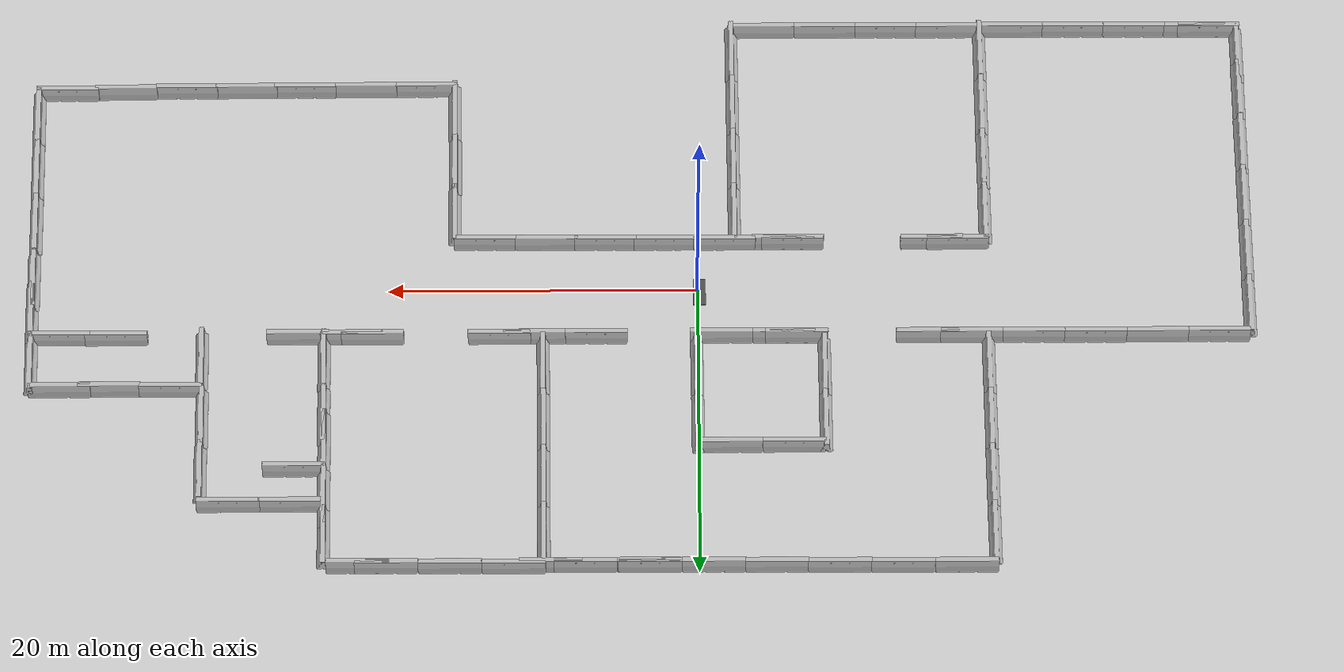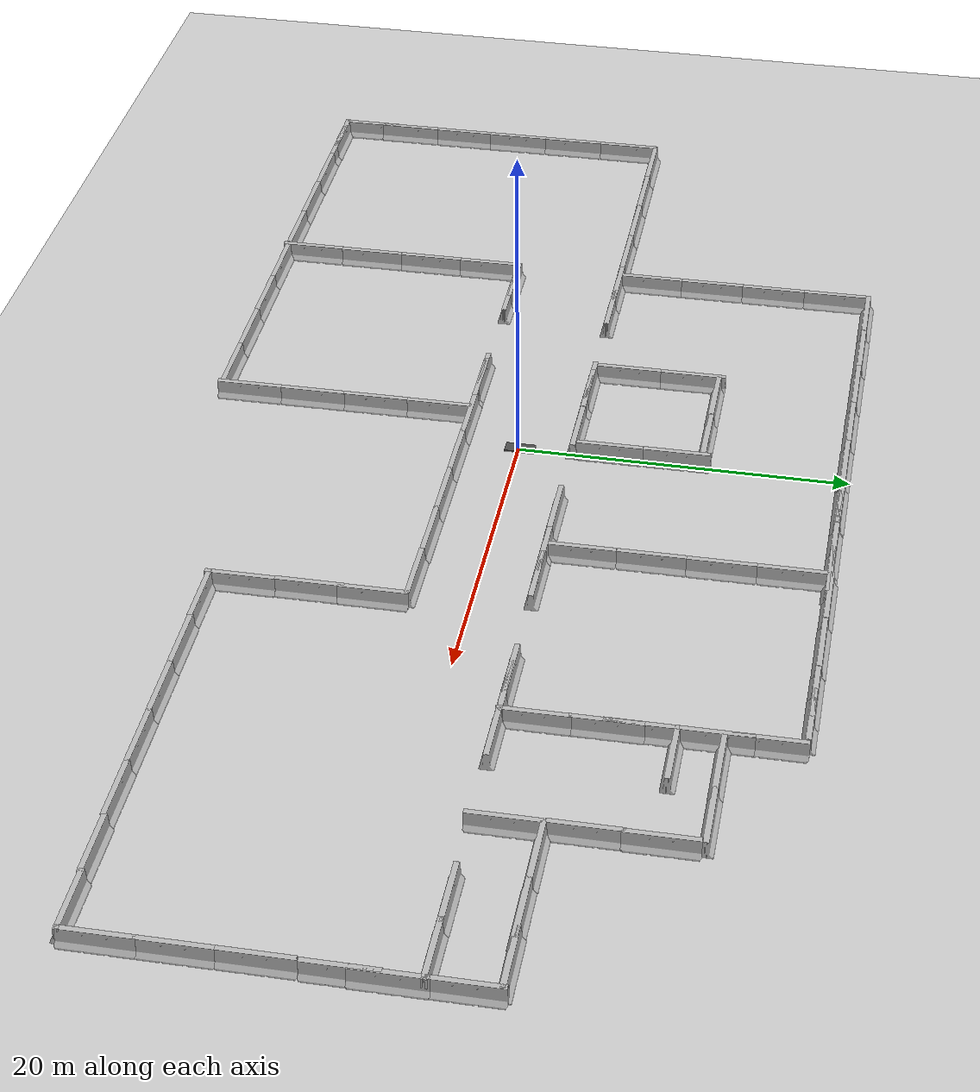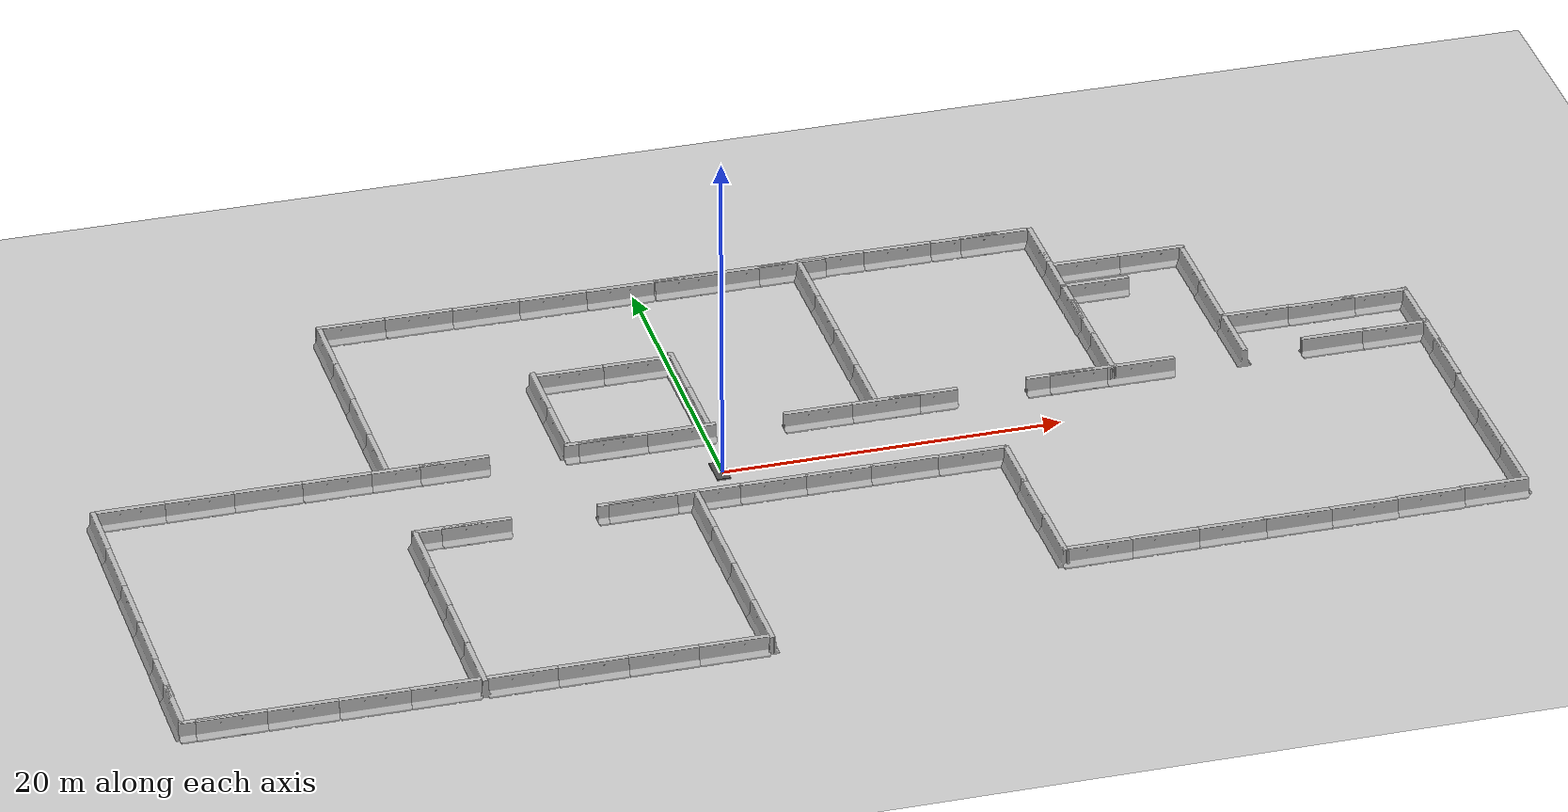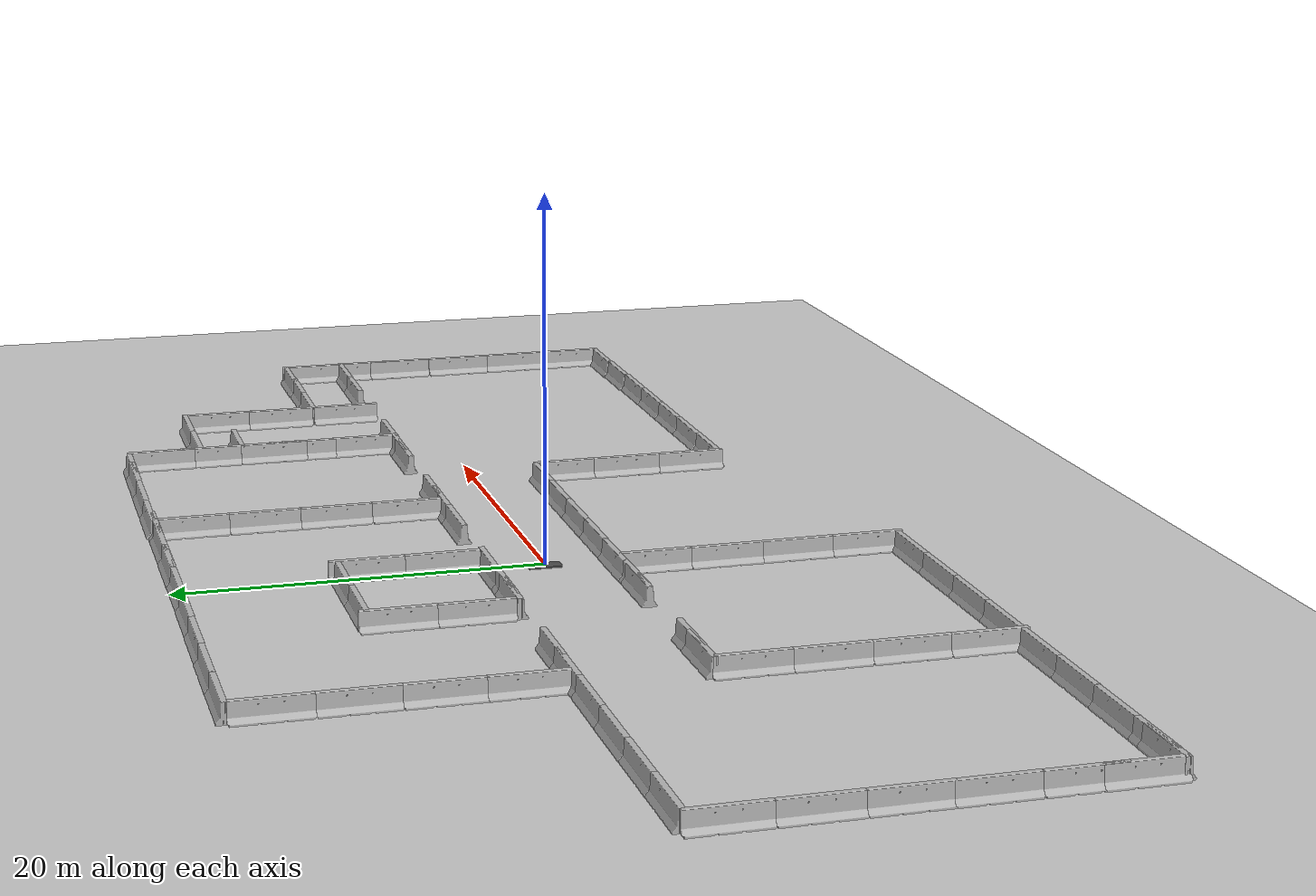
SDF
<sdf version="1.7">
 <world name="default">
  <light name="sun" type="directional">
   <pose>0 0 10 0 -0 0</pose>
   <diffuse>0.8 0.8 0.8 1</diffuse>
   <specular>0.2 0.2 0.2 1</specular>
   <attenuation>
    <range>1000</range>
    <constant>0.9</constant>
    <linear>0.01</linear>
    <quadratic>0.001</quadratic>
   </attenuation>
   <direction>-0.5 0.1 -0.9</direction>
   <spot><inner_angle>0</inner_angle><outer_angle>0</outer_angle><falloff>0</falloff></spot>
  </light>
  <model name="ground_plane">
   <static>1</static>
   <link name="link">
    <collision name="collision">
     <geometry><plane><normal>0 0 1</normal><size>100 100</size></plane></geometry>
     <surface><friction><ode><mu>100</mu><mu2>50</mu2></ode></friction></surface>
    </collision>
    <visual name="visual">
     <cast_shadows>0</cast_shadows>
     <geometry><plane><normal>0 0 1</normal><size>100 100</size></plane></geometry>
     <material>
      <script><uri>file://media/materials/scripts/gazebo.material</uri><name>Gazebo/Grey</name></script>
     </material>
    </visual>
   </link>
  </model>
  <gravity>0 0 -9.8</gravity>
  <magnetic_field>6e-06 2.3e-05 -4.2e-05</magnetic_field>
  <atmosphere type="adiabatic"/>
  <physics type="ode">
   <max_step_size>0.001</max_step_size>
   <real_time_factor>1</real_time_factor>
   <real_time_update_rate>1000</real_time_update_rate>
  </physics>
  <scene><ambient>0.4 0.4 0.4 1</ambient><background>0.7 0.7 0.7 1</background><shadows>1</shadows></scene>
  <audio><device>default</device></audio>
  <spherical_coordinates>
   <surface_model>EARTH_WGS84</surface_model>
   <latitude_deg>0</latitude_deg>
   <longitude_deg>0</longitude_deg>
   <elevation>0</elevation>
   <heading_deg>0</heading_deg>
  </spherical_coordinates>
  <model name="asphalt_plane">
   <static>1</static>
   <link name="link">
    <collision name="collision"><geometry><box><size>0.799213 1.82438 0.1</size></box></geometry></collision>
    <visual name="visual">
     <cast_shadows>0</cast_shadows>
     <geometry><box><size>0.799213 1.82438 0.1</size></box></geometry>
     <material>
      <script>
       <uri>model://asphalt_plane/materials/scripts</uri>
       <uri>model://asphalt_plane/materials/textures</uri>
       <name>vrc/asphalt</name>
      </script>
     </material>
    </visual>
   </link>
   <pose>-0.129245 0.109771 0 0 -0 0</pose>
  </model>
  <model name="jersey_barrier_clone">
   <static>1</static>
   <link name="link">
    <visual name="visual">
     <geometry><mesh><uri>model://jersey_barrier/meshes/jersey_barrier.dae</uri></mesh></geometry>
    </visual>
    <collision name="upright">
     <pose>0 0 0.5715 0 -0 0</pose>
     <geometry><box><size>4.06542 0.3063 1.143</size></box></geometry>
    </collision>
    <collision name="base">
     <pose>0 0 0.032258 0 -0 0</pose>
     <geometry><box><size>4.06542 0.8107 0.064516</size></box></geometry>
    </collision>
    <collision name="base2">
     <pose>0 0 0.1 0 -0 0</pose>
     <geometry><box><size>4.06542 0.65 0.1</size></box></geometry>
    </collision>
    <collision name="base3">
     <pose>0 0 0.2 0 -0 0</pose>
     <geometry><box><size>4.06542 0.5 0.1</size></box></geometry>
    </collision>
    <collision name="left-angle">
     <pose>0 -0.224 0.2401 0.9 -0 0</pose>
     <geometry><box><size>4.06542 0.5 0.064516</size></box></geometry>
    </collision>
    <collision name="right-angle">
     <pose>0 0.224 0.2401 -0.9 0 0</pose>
     <geometry><box><size>4.06542 0.5 0.064516</size></box></geometry>
    </collision>
   </link>
   <pose>-5.58054 -3.36857 0 0 -0 0</pose>
  </model>
  <model name="jersey_barrier_clone_0">
   <static>1</static>
   <link name="link">
    <visual name="visual">
     <geometry><mesh><uri>model://jersey_barrier/meshes/jersey_barrier.dae</uri></mesh></geometry>
    </visual>
    <collision name="upright">
     <pose>0 0 0.5715 0 -0 0</pose>
     <geometry><box><size>4.06542 0.3063 1.143</size></box></geometry>
    </collision>
    <collision name="base">
     <pose>0 0 0.032258 0 -0 0</pose>
     <geometry><box><size>4.06542 0.8107 0.064516</size></box></geometry>
    </collision>
    <collision name="base2">
     <pose>0 0 0.1 0 -0 0</pose>
     <geometry><box><size>4.06542 0.65 0.1</size></box></geometry>
    </collision>
    <collision name="base3">
     <pose>0 0 0.2 0 -0 0</pose>
     <geometry><box><size>4.06542 0.5 0.1</size></box></geometry>
    </collision>
    <collision name="left-angle">
     <pose>0 -0.224 0.2401 0.9 -0 0</pose>
     <geometry><box><size>4.06542 0.5 0.064516</size></box></geometry>
    </collision>
    <collision name="right-angle">
     <pose>0 0.224 0.2401 -0.9 0 0</pose>
     <geometry><box><size>4.06542 0.5 0.064516</size></box></geometry>
    </collision>
   </link>
   <pose>-1.76649 -3.34936 0 0 -0 0</pose>
  </model>
  <model name="jersey_barrier_clone_0_clone_1">
   <static>1</static>
   <link name="link">
    <visual name="visual">
     <geometry><mesh><uri>model://jersey_barrier/meshes/jersey_barrier.dae</uri></mesh></geometry>
    </visual>
    <collision name="upright">
     <pose>0 0 0.5715 0 -0 0</pose>
     <geometry><box><size>4.06542 0.3063 1.143</size></box></geometry>
    </collision>
    <collision name="base">
     <pose>0 0 0.032258 0 -0 0</pose>
     <geometry><box><size>4.06542 0.8107 0.064516</size></box></geometry>
    </collision>
    <collision name="base2">
     <pose>0 0 0.1 0 -0 0</pose>
     <geometry><box><size>4.06542 0.65 0.1</size></box></geometry>
    </collision>
    <collision name="base3">
     <pose>0 0 0.2 0 -0 0</pose>
     <geometry><box><size>4.06542 0.5 0.1</size></box></geometry>
    </collision>
    <collision name="left-angle">
     <pose>0 -0.224 0.2401 0.9 -0 0</pose>
     <geometry><box><size>4.06542 0.5 0.064516</size></box></geometry>
    </collision>
    <collision name="right-angle">
     <pose>0 0.224 0.2401 -0.9 0 0</pose>
     <geometry><box><size>4.06542 0.5 0.064516</size></box></geometry>
    </collision>
   </link>
   <pose>2.09018 -3.3606 0 0 -0 0</pose>
  </model>
  <model name="jersey_barrier_clone_0_clone_2">
   <static>1</static>
   <link name="link">
    <visual name="visual">
     <geometry><mesh><uri>model://jersey_barrier/meshes/jersey_barrier.dae</uri></mesh></geometry>
    </visual>
    <collision name="upright">
     <pose>0 0 0.5715 0 -0 0</pose>
     <geometry><box><size>4.06542 0.3063 1.143</size></box></geometry>
    </collision>
    <collision name="base">
     <pose>0 0 0.032258 0 -0 0</pose>
     <geometry><box><size>4.06542 0.8107 0.064516</size></box></geometry>
    </collision>
    <collision name="base2">
     <pose>0 0 0.1 0 -0 0</pose>
     <geometry><box><size>4.06542 0.65 0.1</size></box></geometry>
    </collision>
    <collision name="base3">
     <pose>0 0 0.2 0 -0 0</pose>
     <geometry><box><size>4.06542 0.5 0.1</size></box></geometry>
    </collision>
    <collision name="left-angle">
     <pose>0 -0.224 0.2401 0.9 -0 0</pose>
     <geometry><box><size>4.06542 0.5 0.064516</size></box></geometry>
    </collision>
    <collision name="right-angle">
     <pose>0 0.224 0.2401 -0.9 0 0</pose>
     <geometry><box><size>4.06542 0.5 0.064516</size></box></geometry>
    </collision>
   </link>
   <pose>5.95957 -3.36203 0 0 -0 0</pose>
  </model>
  <model name="jersey_barrier_clone_0_clone_3">
   <static>1</static>
   <link name="link">
    <visual name="visual">
     <geometry><mesh><uri>model://jersey_barrier/meshes/jersey_barrier.dae</uri></mesh></geometry>
    </visual>
    <collision name="upright">
     <pose>0 0 0.5715 0 -0 0</pose>
     <geometry><box><size>4.06542 0.3063 1.143</size></box></geometry>
    </collision>
    <collision name="base">
     <pose>0 0 0.032258 0 -0 0</pose>
     <geometry><box><size>4.06542 0.8107 0.064516</size></box></geometry>
    </collision>
    <collision name="base2">
     <pose>0 0 0.1 0 -0 0</pose>
     <geometry><box><size>4.06542 0.65 0.1</size></box></geometry>
    </collision>
    <collision name="base3">
     <pose>0 0 0.2 0 -0 0</pose>
     <geometry><box><size>4.06542 0.5 0.1</size></box></geometry>
    </collision>
    <collision name="left-angle">
     <pose>0 -0.224 0.2401 0.9 -0 0</pose>
     <geometry><box><size>4.06542 0.5 0.064516</size></box></geometry>
    </collision>
    <collision name="right-angle">
     <pose>0 0.224 0.2401 -0.9 0 0</pose>
     <geometry><box><size>4.06542 0.5 0.064516</size></box></geometry>
    </collision>
   </link>
   <pose>9.75739 -3.36455 0 0 -0 0</pose>
  </model>
  <model name="jersey_barrier_clone_0_clone_4">
   <static>1</static>
   <link name="link">
    <visual name="visual">
     <geometry><mesh><uri>model://jersey_barrier/meshes/jersey_barrier.dae</uri></mesh></geometry>
    </visual>
    <collision name="upright">
     <pose>0 0 0.5715 0 -0 0</pose>
     <geometry><box><size>4.06542 0.3063 1.143</size></box></geometry>
    </collision>
    <collision name="base">
     <pose>0 0 0.032258 0 -0 0</pose>
     <geometry><box><size>4.06542 0.8107 0.064516</size></box></geometry>
    </collision>
    <collision name="base2">
     <pose>0 0 0.1 0 -0 0</pose>
     <geometry><box><size>4.06542 0.65 0.1</size></box></geometry>
    </collision>
    <collision name="base3">
     <pose>0 0 0.2 0 -0 0</pose>
     <geometry><box><size>4.06542 0.5 0.1</size></box></geometry>
    </collision>
    <collision name="left-angle">
     <pose>0 -0.224 0.2401 0.9 -0 0</pose>
     <geometry><box><size>4.06542 0.5 0.064516</size></box></geometry>
    </collision>
    <collision name="right-angle">
     <pose>0 0.224 0.2401 -0.9 0 0</pose>
     <geometry><box><size>4.06542 0.5 0.064516</size></box></geometry>
    </collision>
   </link>
   <pose>13.7348 -3.39973 0 0 -0 0</pose>
  </model>
  <model name="jersey_barrier_clone_0_clone_0_clone_0">
   <static>1</static>
   <link name="link">
    <visual name="visual">
     <geometry><mesh><uri>model://jersey_barrier/meshes/jersey_barrier.dae</uri></mesh></geometry>
    </visual>
    <collision name="upright">
     <pose>0 0 0.5715 0 -0 0</pose>
     <geometry><box><size>4.06542 0.3063 1.143</size></box></geometry>
    </collision>
    <collision name="base">
     <pose>0 0 0.032258 0 -0 0</pose>
     <geometry><box><size>4.06542 0.8107 0.064516</size></box></geometry>
    </collision>
    <collision name="base2">
     <pose>0 0 0.1 0 -0 0</pose>
     <geometry><box><size>4.06542 0.65 0.1</size></box></geometry>
    </collision>
    <collision name="base3">
     <pose>0 0 0.2 0 -0 0</pose>
     <geometry><box><size>4.06542 0.5 0.1</size></box></geometry>
    </collision>
    <collision name="left-angle">
     <pose>0 -0.224 0.2401 0.9 -0 0</pose>
     <geometry><box><size>4.06542 0.5 0.064516</size></box></geometry>
    </collision>
    <collision name="right-angle">
     <pose>0 0.224 0.2401 -0.9 0 0</pose>
     <geometry><box><size>4.06542 0.5 0.064516</size></box></geometry>
    </collision>
   </link>
   <pose>15.7986 -12.9502 0 0 0 -1.56339</pose>
  </model>
  <model name="jersey_barrier_clone_0_clone_4_clone">
   <static>1</static>
   <link name="link">
    <visual name="visual">
     <geometry><mesh><uri>model://jersey_barrier/meshes/jersey_barrier.dae</uri></mesh></geometry>
    </visual>
    <collision name="upright">
     <pose>0 0 0.5715 0 -0 0</pose>
     <geometry><box><size>4.06542 0.3063 1.143</size></box></geometry>
    </collision>
    <collision name="base">
     <pose>0 0 0.032258 0 -0 0</pose>
     <geometry><box><size>4.06542 0.8107 0.064516</size></box></geometry>
    </collision>
    <collision name="base2">
     <pose>0 0 0.1 0 -0 0</pose>
     <geometry><box><size>4.06542 0.65 0.1</size></box></geometry>
    </collision>
    <collision name="base3">
     <pose>0 0 0.2 0 -0 0</pose>
     <geometry><box><size>4.06542 0.5 0.1</size></box></geometry>
    </collision>
    <collision name="left-angle">
     <pose>0 -0.224 0.2401 0.9 -0 0</pose>
     <geometry><box><size>4.06542 0.5 0.064516</size></box></geometry>
    </collision>
    <collision name="right-angle">
     <pose>0 0.224 0.2401 -0.9 0 0</pose>
     <geometry><box><size>4.06542 0.5 0.064516</size></box></geometry>
    </collision>
   </link>
   <pose>17.705 -14.7157 0 0 -0 0</pose>
  </model>
  <model name="jersey_barrier_clone_0_clone_4_clone_0">
   <static>1</static>
   <link name="link">
    <visual name="visual">
     <geometry><mesh><uri>model://jersey_barrier/meshes/jersey_barrier.dae</uri></mesh></geometry>
    </visual>
    <collision name="upright">
     <pose>0 0 0.5715 0 -0 0</pose>
     <geometry><box><size>4.06542 0.3063 1.143</size></box></geometry>
    </collision>
    <collision name="base">
     <pose>0 0 0.032258 0 -0 0</pose>
     <geometry><box><size>4.06542 0.8107 0.064516</size></box></geometry>
    </collision>
    <collision name="base2">
     <pose>0 0 0.1 0 -0 0</pose>
     <geometry><box><size>4.06542 0.65 0.1</size></box></geometry>
    </collision>
    <collision name="base3">
     <pose>0 0 0.2 0 -0 0</pose>
     <geometry><box><size>4.06542 0.5 0.1</size></box></geometry>
    </collision>
    <collision name="left-angle">
     <pose>0 -0.224 0.2401 0.9 -0 0</pose>
     <geometry><box><size>4.06542 0.5 0.064516</size></box></geometry>
    </collision>
    <collision name="right-angle">
     <pose>0 0.224 0.2401 -0.9 0 0</pose>
     <geometry><box><size>4.06542 0.5 0.064516</size></box></geometry>
    </collision>
   </link>
   <pose>21.6479 -14.684 0 0 -0 0</pose>
  </model>
  <model name="jersey_barrier_clone_0_clone_4_clone_1">
   <static>1</static>
   <link name="link">
    <visual name="visual">
     <geometry><mesh><uri>model://jersey_barrier/meshes/jersey_barrier.dae</uri></mesh></geometry>
    </visual>
    <collision name="upright">
     <pose>0 0 0.5715 0 -0 0</pose>
     <geometry><box><size>4.06542 0.3063 1.143</size></box></geometry>
    </collision>
    <collision name="base">
     <pose>0 0 0.032258 0 -0 0</pose>
     <geometry><box><size>4.06542 0.8107 0.064516</size></box></geometry>
    </collision>
    <collision name="base2">
     <pose>0 0 0.1 0 -0 0</pose>
     <geometry><box><size>4.06542 0.65 0.1</size></box></geometry>
    </collision>
    <collision name="base3">
     <pose>0 0 0.2 0 -0 0</pose>
     <geometry><box><size>4.06542 0.5 0.1</size></box></geometry>
    </collision>
    <collision name="left-angle">
     <pose>0 -0.224 0.2401 0.9 -0 0</pose>
     <geometry><box><size>4.06542 0.5 0.064516</size></box></geometry>
    </collision>
    <collision name="right-angle">
     <pose>0 0.224 0.2401 -0.9 0 0</pose>
     <geometry><box><size>4.06542 0.5 0.064516</size></box></geometry>
    </collision>
   </link>
   <pose>25.6132 -14.6676 0 0 -0 0</pose>
  </model>
  <model name="jersey_barrier_clone_0_clone_4_clone_2">
   <static>1</static>
   <link name="link">
    <visual name="visual">
     <geometry><mesh><uri>model://jersey_barrier/meshes/jersey_barrier.dae</uri></mesh></geometry>
    </visual>
    <collision name="upright">
     <pose>0 0 0.5715 0 -0 0</pose>
     <geometry><box><size>4.06542 0.3063 1.143</size></box></geometry>
    </collision>
    <collision name="base">
     <pose>0 0 0.032258 0 -0 0</pose>
     <geometry><box><size>4.06542 0.8107 0.064516</size></box></geometry>
    </collision>
    <collision name="base2">
     <pose>0 0 0.1 0 -0 0</pose>
     <geometry><box><size>4.06542 0.65 0.1</size></box></geometry>
    </collision>
    <collision name="base3">
     <pose>0 0 0.2 0 -0 0</pose>
     <geometry><box><size>4.06542 0.5 0.1</size></box></geometry>
    </collision>
    <collision name="left-angle">
     <pose>0 -0.224 0.2401 0.9 -0 0</pose>
     <geometry><box><size>4.06542 0.5 0.064516</size></box></geometry>
    </collision>
    <collision name="right-angle">
     <pose>0 0.224 0.2401 -0.9 0 0</pose>
     <geometry><box><size>4.06542 0.5 0.064516</size></box></geometry>
    </collision>
   </link>
   <pose>29.4672 -14.6534 0 0 -0 0</pose>
  </model>
  <model name="jersey_barrier_clone_0_clone_4_clone_3">
   <static>1</static>
   <link name="link">
    <visual name="visual">
     <geometry><mesh><uri>model://jersey_barrier/meshes/jersey_barrier.dae</uri></mesh></geometry>
    </visual>
    <collision name="upright">
     <pose>0 0 0.5715 0 -0 0</pose>
     <geometry><box><size>4.06542 0.3063 1.143</size></box></geometry>
    </collision>
    <collision name="base">
     <pose>0 0 0.032258 0 -0 0</pose>
     <geometry><box><size>4.06542 0.8107 0.064516</size></box></geometry>
    </collision>
    <collision name="base2">
     <pose>0 0 0.1 0 -0 0</pose>
     <geometry><box><size>4.06542 0.65 0.1</size></box></geometry>
    </collision>
    <collision name="base3">
     <pose>0 0 0.2 0 -0 0</pose>
     <geometry><box><size>4.06542 0.5 0.1</size></box></geometry>
    </collision>
    <collision name="left-angle">
     <pose>0 -0.224 0.2401 0.9 -0 0</pose>
     <geometry><box><size>4.06542 0.5 0.064516</size></box></geometry>
    </collision>
    <collision name="right-angle">
     <pose>0 0.224 0.2401 -0.9 0 0</pose>
     <geometry><box><size>4.06542 0.5 0.064516</size></box></geometry>
    </collision>
   </link>
   <pose>33.3765 -14.6389 0 0 -0 0</pose>
  </model>
  <model name="jersey_barrier_clone_0_clone_4_clone_3_clone">
   <static>1</static>
   <link name="link">
    <visual name="visual">
     <geometry><mesh><uri>model://jersey_barrier/meshes/jersey_barrier.dae</uri></mesh></geometry>
    </visual>
    <collision name="upright">
     <pose>0 0 0.5715 0 -0 0</pose>
     <geometry><box><size>4.06542 0.3063 1.143</size></box></geometry>
    </collision>
    <collision name="base">
     <pose>0 0 0.032258 0 -0 0</pose>
     <geometry><box><size>4.06542 0.8107 0.064516</size></box></geometry>
    </collision>
    <collision name="base2">
     <pose>0 0 0.1 0 -0 0</pose>
     <geometry><box><size>4.06542 0.65 0.1</size></box></geometry>
    </collision>
    <collision name="base3">
     <pose>0 0 0.2 0 -0 0</pose>
     <geometry><box><size>4.06542 0.5 0.1</size></box></geometry>
    </collision>
    <collision name="left-angle">
     <pose>0 -0.224 0.2401 0.9 -0 0</pose>
     <geometry><box><size>4.06542 0.5 0.064516</size></box></geometry>
    </collision>
    <collision name="right-angle">
     <pose>0 0.224 0.2401 -0.9 0 0</pose>
     <geometry><box><size>4.06542 0.5 0.064516</size></box></geometry>
    </collision>
   </link>
   <pose>37.3448 -14.5673 0 0 -0 0</pose>
  </model>
  <model name="jersey_barrier_clone_0_clone_0_clone_0_clone">
   <static>1</static>
   <link name="link">
    <visual name="visual">
     <geometry><mesh><uri>model://jersey_barrier/meshes/jersey_barrier.dae</uri></mesh></geometry>
    </visual>
    <collision name="upright">
     <pose>0 0 0.5715 0 -0 0</pose>
     <geometry><box><size>4.06542 0.3063 1.143</size></box></geometry>
    </collision>
    <collision name="base">
     <pose>0 0 0.032258 0 -0 0</pose>
     <geometry><box><size>4.06542 0.8107 0.064516</size></box></geometry>
    </collision>
    <collision name="base2">
     <pose>0 0 0.1 0 -0 0</pose>
     <geometry><box><size>4.06542 0.65 0.1</size></box></geometry>
    </collision>
    <collision name="base3">
     <pose>0 0 0.2 0 -0 0</pose>
     <geometry><box><size>4.06542 0.5 0.1</size></box></geometry>
    </collision>
    <collision name="left-angle">
     <pose>0 -0.224 0.2401 0.9 -0 0</pose>
     <geometry><box><size>4.06542 0.5 0.064516</size></box></geometry>
    </collision>
    <collision name="right-angle">
     <pose>0 0.224 0.2401 -0.9 0 0</pose>
     <geometry><box><size>4.06542 0.5 0.064516</size></box></geometry>
    </collision>
   </link>
   <pose>15.7344 -8.96603 0 0 0 -1.56339</pose>
  </model>
  <model name="jersey_barrier_clone_0_clone_0_clone_0_clone_0">
   <static>1</static>
   <link name="link">
    <visual name="visual">
     <geometry><mesh><uri>model://jersey_barrier/meshes/jersey_barrier.dae</uri></mesh></geometry>
    </visual>
    <collision name="upright">
     <pose>0 0 0.5715 0 -0 0</pose>
     <geometry><box><size>4.06542 0.3063 1.143</size></box></geometry>
    </collision>
    <collision name="base">
     <pose>0 0 0.032258 0 -0 0</pose>
     <geometry><box><size>4.06542 0.8107 0.064516</size></box></geometry>
    </collision>
    <collision name="base2">
     <pose>0 0 0.1 0 -0 0</pose>
     <geometry><box><size>4.06542 0.65 0.1</size></box></geometry>
    </collision>
    <collision name="base3">
     <pose>0 0 0.2 0 -0 0</pose>
     <geometry><box><size>4.06542 0.5 0.1</size></box></geometry>
    </collision>
    <collision name="left-angle">
     <pose>0 -0.224 0.2401 0.9 -0 0</pose>
     <geometry><box><size>4.06542 0.5 0.064516</size></box></geometry>
    </collision>
    <collision name="right-angle">
     <pose>0 0.224 0.2401 -0.9 0 0</pose>
     <geometry><box><size>4.06542 0.5 0.064516</size></box></geometry>
    </collision>
   </link>
   <pose>15.7362 -5.33956 0 0 0 -1.56339</pose>
  </model>
  <model name="jersey_barrier_clone_0_clone_4_clone_4">
   <static>1</static>
   <link name="link">
    <visual name="visual">
     <geometry><mesh><uri>model://jersey_barrier/meshes/jersey_barrier.dae</uri></mesh></geometry>
    </visual>
    <collision name="upright">
     <pose>0 0 0.5715 0 -0 0</pose>
     <geometry><box><size>4.06542 0.3063 1.143</size></box></geometry>
    </collision>
    <collision name="base">
     <pose>0 0 0.032258 0 -0 0</pose>
     <geometry><box><size>4.06542 0.8107 0.064516</size></box></geometry>
    </collision>
    <collision name="base2">
     <pose>0 0 0.1 0 -0 0</pose>
     <geometry><box><size>4.06542 0.65 0.1</size></box></geometry>
    </collision>
    <collision name="base3">
     <pose>0 0 0.2 0 -0 0</pose>
     <geometry><box><size>4.06542 0.5 0.1</size></box></geometry>
    </collision>
    <collision name="left-angle">
     <pose>0 -0.224 0.2401 0.9 -0 0</pose>
     <geometry><box><size>4.06542 0.5 0.064516</size></box></geometry>
    </collision>
    <collision name="right-angle">
     <pose>0 0.224 0.2401 -0.9 0 0</pose>
     <geometry><box><size>4.06542 0.5 0.064516</size></box></geometry>
    </collision>
   </link>
   <pose>41.169 -14.4988 0 0 -0 0</pose>
  </model>
  <model name="jersey_barrier_clone_0_clone_4_clone_6">
   <static>1</static>
   <link name="link">
    <visual name="visual">
     <geometry><mesh><uri>model://jersey_barrier/meshes/jersey_barrier.dae</uri></mesh></geometry>
    </visual>
    <collision name="upright">
     <pose>0 0 0.5715 0 -0 0</pose>
     <geometry><box><size>4.06542 0.3063 1.143</size></box></geometry>
    </collision>
    <collision name="base">
     <pose>0 0 0.032258 0 -0 0</pose>
     <geometry><box><size>4.06542 0.8107 0.064516</size></box></geometry>
    </collision>
    <collision name="base2">
     <pose>0 0 0.1 0 -0 0</pose>
     <geometry><box><size>4.06542 0.65 0.1</size></box></geometry>
    </collision>
    <collision name="base3">
     <pose>0 0 0.2 0 -0 0</pose>
     <geometry><box><size>4.06542 0.5 0.1</size></box></geometry>
    </collision>
    <collision name="left-angle">
     <pose>0 -0.224 0.2401 0.9 -0 0</pose>
     <geometry><box><size>4.06542 0.5 0.064516</size></box></geometry>
    </collision>
    <collision name="right-angle">
     <pose>0 0.224 0.2401 -0.9 0 0</pose>
     <geometry><box><size>4.06542 0.5 0.064516</size></box></geometry>
    </collision>
   </link>
   <pose>41.1611 3.41587 0 0 -0 0</pose>
  </model>
  <model name="jersey_barrier_clone_0_clone_4_clone_7">
   <static>1</static>
   <link name="link">
    <visual name="visual">
     <geometry><mesh><uri>model://jersey_barrier/meshes/jersey_barrier.dae</uri></mesh></geometry>
    </visual>
    <collision name="upright">
     <pose>0 0 0.5715 0 -0 0</pose>
     <geometry><box><size>4.06542 0.3063 1.143</size></box></geometry>
    </collision>
    <collision name="base">
     <pose>0 0 0.032258 0 -0 0</pose>
     <geometry><box><size>4.06542 0.8107 0.064516</size></box></geometry>
    </collision>
    <collision name="base2">
     <pose>0 0 0.1 0 -0 0</pose>
     <geometry><box><size>4.06542 0.65 0.1</size></box></geometry>
    </collision>
    <collision name="base3">
     <pose>0 0 0.2 0 -0 0</pose>
     <geometry><box><size>4.06542 0.5 0.1</size></box></geometry>
    </collision>
    <collision name="left-angle">
     <pose>0 -0.224 0.2401 0.9 -0 0</pose>
     <geometry><box><size>4.06542 0.5 0.064516</size></box></geometry>
    </collision>
    <collision name="right-angle">
     <pose>0 0.224 0.2401 -0.9 0 0</pose>
     <geometry><box><size>4.06542 0.5 0.064516</size></box></geometry>
    </collision>
   </link>
   <pose>37.4892 3.43491 0 0 -0 0</pose>
  </model>
  <model name="jersey_barrier_clone_0_clone_0_clone_0_clone_0_clone">
   <static>1</static>
   <link name="link">
    <visual name="visual">
     <geometry><mesh><uri>model://jersey_barrier/meshes/jersey_barrier.dae</uri></mesh></geometry>
    </visual>
    <collision name="upright">
     <pose>0 0 0.5715 0 -0 0</pose>
     <geometry><box><size>4.06542 0.3063 1.143</size></box></geometry>
    </collision>
    <collision name="base">
     <pose>0 0 0.032258 0 -0 0</pose>
     <geometry><box><size>4.06542 0.8107 0.064516</size></box></geometry>
    </collision>
    <collision name="base2">
     <pose>0 0 0.1 0 -0 0</pose>
     <geometry><box><size>4.06542 0.65 0.1</size></box></geometry>
    </collision>
    <collision name="base3">
     <pose>0 0 0.2 0 -0 0</pose>
     <geometry><box><size>4.06542 0.5 0.1</size></box></geometry>
    </collision>
    <collision name="left-angle">
     <pose>0 -0.224 0.2401 0.9 -0 0</pose>
     <geometry><box><size>4.06542 0.5 0.064516</size></box></geometry>
    </collision>
    <collision name="right-angle">
     <pose>0 0.224 0.2401 -0.9 0 0</pose>
     <geometry><box><size>4.06542 0.5 0.064516</size></box></geometry>
    </collision>
   </link>
   <pose>43.0252 -12.5774 0 0 0 -1.56339</pose>
  </model>
  <model name="jersey_barrier_clone_0_clone_0_clone_0_clone_0_clone_0">
   <static>1</static>
   <link name="link">
    <visual name="visual">
     <geometry><mesh><uri>model://jersey_barrier/meshes/jersey_barrier.dae</uri></mesh></geometry>
    </visual>
    <collision name="upright">
     <pose>0 0 0.5715 0 -0 0</pose>
     <geometry><box><size>4.06542 0.3063 1.143</size></box></geometry>
    </collision>
    <collision name="base">
     <pose>0 0 0.032258 0 -0 0</pose>
     <geometry><box><size>4.06542 0.8107 0.064516</size></box></geometry>
    </collision>
    <collision name="base2">
     <pose>0 0 0.1 0 -0 0</pose>
     <geometry><box><size>4.06542 0.65 0.1</size></box></geometry>
    </collision>
    <collision name="base3">
     <pose>0 0 0.2 0 -0 0</pose>
     <geometry><box><size>4.06542 0.5 0.1</size></box></geometry>
    </collision>
    <collision name="left-angle">
     <pose>0 -0.224 0.2401 0.9 -0 0</pose>
     <geometry><box><size>4.06542 0.5 0.064516</size></box></geometry>
    </collision>
    <collision name="right-angle">
     <pose>0 0.224 0.2401 -0.9 0 0</pose>
     <geometry><box><size>4.06542 0.5 0.064516</size></box></geometry>
    </collision>
   </link>
   <pose>42.9941 -8.71312 0 0 0 -1.56339</pose>
  </model>
  <model name="jersey_barrier_clone_0_clone_0_clone_0_clone_0_clone_1">
   <static>1</static>
   <link name="link">
    <visual name="visual">
     <geometry><mesh><uri>model://jersey_barrier/meshes/jersey_barrier.dae</uri></mesh></geometry>
    </visual>
    <collision name="upright">
     <pose>0 0 0.5715 0 -0 0</pose>
     <geometry><box><size>4.06542 0.3063 1.143</size></box></geometry>
    </collision>
    <collision name="base">
     <pose>0 0 0.032258 0 -0 0</pose>
     <geometry><box><size>4.06542 0.8107 0.064516</size></box></geometry>
    </collision>
    <collision name="base2">
     <pose>0 0 0.1 0 -0 0</pose>
     <geometry><box><size>4.06542 0.65 0.1</size></box></geometry>
    </collision>
    <collision name="base3">
     <pose>0 0 0.2 0 -0 0</pose>
     <geometry><box><size>4.06542 0.5 0.1</size></box></geometry>
    </collision>
    <collision name="left-angle">
     <pose>0 -0.224 0.2401 0.9 -0 0</pose>
     <geometry><box><size>4.06542 0.5 0.064516</size></box></geometry>
    </collision>
    <collision name="right-angle">
     <pose>0 0.224 0.2401 -0.9 0 0</pose>
     <geometry><box><size>4.06542 0.5 0.064516</size></box></geometry>
    </collision>
   </link>
   <pose>42.9568 -4.73014 0 0 0 -1.56339</pose>
  </model>
  <model name="jersey_barrier_clone_0_clone_0_clone_0_clone_0_clone_2">
   <static>1</static>
   <link name="link">
    <visual name="visual">
     <geometry><mesh><uri>model://jersey_barrier/meshes/jersey_barrier.dae</uri></mesh></geometry>
    </visual>
    <collision name="upright">
     <pose>0 0 0.5715 0 -0 0</pose>
     <geometry><box><size>4.06542 0.3063 1.143</size></box></geometry>
    </collision>
    <collision name="base">
     <pose>0 0 0.032258 0 -0 0</pose>
     <geometry><box><size>4.06542 0.8107 0.064516</size></box></geometry>
    </collision>
    <collision name="base2">
     <pose>0 0 0.1 0 -0 0</pose>
     <geometry><box><size>4.06542 0.65 0.1</size></box></geometry>
    </collision>
    <collision name="base3">
     <pose>0 0 0.2 0 -0 0</pose>
     <geometry><box><size>4.06542 0.5 0.1</size></box></geometry>
    </collision>
    <collision name="left-angle">
     <pose>0 -0.224 0.2401 0.9 -0 0</pose>
     <geometry><box><size>4.06542 0.5 0.064516</size></box></geometry>
    </collision>
    <collision name="right-angle">
     <pose>0 0.224 0.2401 -0.9 0 0</pose>
     <geometry><box><size>4.06542 0.5 0.064516</size></box></geometry>
    </collision>
   </link>
   <pose>42.9791 -0.627617 0 0 0 -1.56339</pose>
  </model>
  <model name="jersey_barrier_clone_0_clone_0_clone_0_clone_0_clone_3">
   <static>1</static>
   <link name="link">
    <visual name="visual">
     <geometry><mesh><uri>model://jersey_barrier/meshes/jersey_barrier.dae</uri></mesh></geometry>
    </visual>
    <collision name="upright">
     <pose>0 0 0.5715 0 -0 0</pose>
     <geometry><box><size>4.06542 0.3063 1.143</size></box></geometry>
    </collision>
    <collision name="base">
     <pose>0 0 0.032258 0 -0 0</pose>
     <geometry><box><size>4.06542 0.8107 0.064516</size></box></geometry>
    </collision>
    <collision name="base2">
     <pose>0 0 0.1 0 -0 0</pose>
     <geometry><box><size>4.06542 0.65 0.1</size></box></geometry>
    </collision>
    <collision name="base3">
     <pose>0 0 0.2 0 -0 0</pose>
     <geometry><box><size>4.06542 0.5 0.1</size></box></geometry>
    </collision>
    <collision name="left-angle">
     <pose>0 -0.224 0.2401 0.9 -0 0</pose>
     <geometry><box><size>4.06542 0.5 0.064516</size></box></geometry>
    </collision>
    <collision name="right-angle">
     <pose>0 0.224 0.2401 -0.9 0 0</pose>
     <geometry><box><size>4.06542 0.5 0.064516</size></box></geometry>
    </collision>
   </link>
   <pose>43.0136 1.69115 0 0 0 -1.56339</pose>
  </model>
  <model name="jersey_barrier_clone_0_clone_0_clone_0_clone_0_clone_2_clone">
   <static>1</static>
   <link name="link">
    <visual name="visual">
     <geometry><mesh><uri>model://jersey_barrier/meshes/jersey_barrier.dae</uri></mesh></geometry>
    </visual>
    <collision name="upright">
     <pose>0 0 0.5715 0 -0 0</pose>
     <geometry><box><size>4.06542 0.3063 1.143</size></box></geometry>
    </collision>
    <collision name="base">
     <pose>0 0 0.032258 0 -0 0</pose>
     <geometry><box><size>4.06542 0.8107 0.064516</size></box></geometry>
    </collision>
    <collision name="base2">
     <pose>0 0 0.1 0 -0 0</pose>
     <geometry><box><size>4.06542 0.65 0.1</size></box></geometry>
    </collision>
    <collision name="base3">
     <pose>0 0 0.2 0 -0 0</pose>
     <geometry><box><size>4.06542 0.5 0.1</size></box></geometry>
    </collision>
    <collision name="left-angle">
     <pose>0 -0.224 0.2401 0.9 -0 0</pose>
     <geometry><box><size>4.06542 0.5 0.064516</size></box></geometry>
    </collision>
    <collision name="right-angle">
     <pose>0 0.224 0.2401 -0.9 0 0</pose>
     <geometry><box><size>4.06542 0.5 0.064516</size></box></geometry>
    </collision>
   </link>
   <pose>42.9652 5.36529 0 0 0 -1.56339</pose>
  </model>
  <model name="jersey_barrier_clone_0_clone_4_clone_7_clone">
   <static>1</static>
   <link name="link">
    <visual name="visual">
     <geometry><mesh><uri>model://jersey_barrier/meshes/jersey_barrier.dae</uri></mesh></geometry>
    </visual>
    <collision name="upright">
     <pose>0 0 0.5715 0 -0 0</pose>
     <geometry><box><size>4.06542 0.3063 1.143</size></box></geometry>
    </collision>
    <collision name="base">
     <pose>0 0 0.032258 0 -0 0</pose>
     <geometry><box><size>4.06542 0.8107 0.064516</size></box></geometry>
    </collision>
    <collision name="base2">
     <pose>0 0 0.1 0 -0 0</pose>
     <geometry><box><size>4.06542 0.65 0.1</size></box></geometry>
    </collision>
    <collision name="base3">
     <pose>0 0 0.2 0 -0 0</pose>
     <geometry><box><size>4.06542 0.5 0.1</size></box></geometry>
    </collision>
    <collision name="left-angle">
     <pose>0 -0.224 0.2401 0.9 -0 0</pose>
     <geometry><box><size>4.06542 0.5 0.064516</size></box></geometry>
    </collision>
    <collision name="right-angle">
     <pose>0 0.224 0.2401 -0.9 0 0</pose>
     <geometry><box><size>4.06542 0.5 0.064516</size></box></geometry>
    </collision>
   </link>
   <pose>33.8913 7.13913 0 0 -0 0</pose>
  </model>
  <model name="jersey_barrier_clone_0_clone_0_clone_0_clone_0_clone_2_clone_clone">
   <static>1</static>
   <link name="link">
    <visual name="visual">
     <geometry><mesh><uri>model://jersey_barrier/meshes/jersey_barrier.dae</uri></mesh></geometry>
    </visual>
    <collision name="upright">
     <pose>0 0 0.5715 0 -0 0</pose>
     <geometry><box><size>4.06542 0.3063 1.143</size></box></geometry>
    </collision>
    <collision name="base">
     <pose>0 0 0.032258 0 -0 0</pose>
     <geometry><box><size>4.06542 0.8107 0.064516</size></box></geometry>
    </collision>
    <collision name="base2">
     <pose>0 0 0.1 0 -0 0</pose>
     <geometry><box><size>4.06542 0.65 0.1</size></box></geometry>
    </collision>
    <collision name="base3">
     <pose>0 0 0.2 0 -0 0</pose>
     <geometry><box><size>4.06542 0.5 0.1</size></box></geometry>
    </collision>
    <collision name="left-angle">
     <pose>0 -0.224 0.2401 0.9 -0 0</pose>
     <geometry><box><size>4.06542 0.5 0.064516</size></box></geometry>
    </collision>
    <collision name="right-angle">
     <pose>0 0.224 0.2401 -0.9 0 0</pose>
     <geometry><box><size>4.06542 0.5 0.064516</size></box></geometry>
    </collision>
   </link>
   <pose>31.945 5.08337 0 0 0 -1.56339</pose>
  </model>
  <model name="jersey_barrier_clone_0_clone_0_clone_0_clone_0_clone_2_clone_clone_0">
   <static>1</static>
   <link name="link">
    <visual name="visual">
     <geometry><mesh><uri>model://jersey_barrier/meshes/jersey_barrier.dae</uri></mesh></geometry>
    </visual>
    <collision name="upright">
     <pose>0 0 0.5715 0 -0 0</pose>
     <geometry><box><size>4.06542 0.3063 1.143</size></box></geometry>
    </collision>
    <collision name="base">
     <pose>0 0 0.032258 0 -0 0</pose>
     <geometry><box><size>4.06542 0.8107 0.064516</size></box></geometry>
    </collision>
    <collision name="base2">
     <pose>0 0 0.1 0 -0 0</pose>
     <geometry><box><size>4.06542 0.65 0.1</size></box></geometry>
    </collision>
    <collision name="base3">
     <pose>0 0 0.2 0 -0 0</pose>
     <geometry><box><size>4.06542 0.5 0.1</size></box></geometry>
    </collision>
    <collision name="left-angle">
     <pose>0 -0.224 0.2401 0.9 -0 0</pose>
     <geometry><box><size>4.06542 0.5 0.064516</size></box></geometry>
    </collision>
    <collision name="right-angle">
     <pose>0 0.224 0.2401 -0.9 0 0</pose>
     <geometry><box><size>4.06542 0.5 0.064516</size></box></geometry>
    </collision>
   </link>
   <pose>31.8669 9.24831 0 0 0 -1.56339</pose>
  </model>
  <model name="jersey_barrier_clone_0_clone_4_clone_7_clone_clone">
   <static>1</static>
   <link name="link">
    <visual name="visual">
     <geometry><mesh><uri>model://jersey_barrier/meshes/jersey_barrier.dae</uri></mesh></geometry>
    </visual>
    <collision name="upright">
     <pose>0 0 0.5715 0 -0 0</pose>
     <geometry><box><size>4.06542 0.3063 1.143</size></box></geometry>
    </collision>
    <collision name="base">
     <pose>0 0 0.032258 0 -0 0</pose>
     <geometry><box><size>4.06542 0.8107 0.064516</size></box></geometry>
    </collision>
    <collision name="base2">
     <pose>0 0 0.1 0 -0 0</pose>
     <geometry><box><size>4.06542 0.65 0.1</size></box></geometry>
    </collision>
    <collision name="base3">
     <pose>0 0 0.2 0 -0 0</pose>
     <geometry><box><size>4.06542 0.5 0.1</size></box></geometry>
    </collision>
    <collision name="left-angle">
     <pose>0 -0.224 0.2401 0.9 -0 0</pose>
     <geometry><box><size>4.06542 0.5 0.064516</size></box></geometry>
    </collision>
    <collision name="right-angle">
     <pose>0 0.224 0.2401 -0.9 0 0</pose>
     <geometry><box><size>4.06542 0.5 0.064516</size></box></geometry>
    </collision>
   </link>
   <pose>37.8213 7.10404 0 0 -0 0</pose>
  </model>
  <model name="jersey_barrier_clone_0_clone_4_clone_7_clone_clone_clone">
   <static>1</static>
   <link name="link">
    <visual name="visual">
     <geometry><mesh><uri>model://jersey_barrier/meshes/jersey_barrier.dae</uri></mesh></geometry>
    </visual>
    <collision name="upright">
     <pose>0 0 0.5715 0 -0 0</pose>
     <geometry><box><size>4.06542 0.3063 1.143</size></box></geometry>
    </collision>
    <collision name="base">
     <pose>0 0 0.032258 0 -0 0</pose>
     <geometry><box><size>4.06542 0.8107 0.064516</size></box></geometry>
    </collision>
    <collision name="base2">
     <pose>0 0 0.1 0 -0 0</pose>
     <geometry><box><size>4.06542 0.65 0.1</size></box></geometry>
    </collision>
    <collision name="base3">
     <pose>0 0 0.2 0 -0 0</pose>
     <geometry><box><size>4.06542 0.5 0.1</size></box></geometry>
    </collision>
    <collision name="left-angle">
     <pose>0 -0.224 0.2401 0.9 -0 0</pose>
     <geometry><box><size>4.06542 0.5 0.064516</size></box></geometry>
    </collision>
    <collision name="right-angle">
     <pose>0 0.224 0.2401 -0.9 0 0</pose>
     <geometry><box><size>4.06542 0.5 0.064516</size></box></geometry>
    </collision>
   </link>
   <pose>41.0499 7.14349 0 0 -0 0</pose>
  </model>
  <model name="jersey_barrier_clone_0_clone_4_clone_7_clone_2">
   <static>1</static>
   <link name="link">
    <visual name="visual">
     <geometry><mesh><uri>model://jersey_barrier/meshes/jersey_barrier.dae</uri></mesh></geometry>
    </visual>
    <collision name="upright">
     <pose>0 0 0.5715 0 -0 0</pose>
     <geometry><box><size>4.06542 0.3063 1.143</size></box></geometry>
    </collision>
    <collision name="base">
     <pose>0 0 0.032258 0 -0 0</pose>
     <geometry><box><size>4.06542 0.8107 0.064516</size></box></geometry>
    </collision>
    <collision name="base2">
     <pose>0 0 0.1 0 -0 0</pose>
     <geometry><box><size>4.06542 0.65 0.1</size></box></geometry>
    </collision>
    <collision name="base3">
     <pose>0 0 0.2 0 -0 0</pose>
     <geometry><box><size>4.06542 0.5 0.1</size></box></geometry>
    </collision>
    <collision name="left-angle">
     <pose>0 -0.224 0.2401 0.9 -0 0</pose>
     <geometry><box><size>4.06542 0.5 0.064516</size></box></geometry>
    </collision>
    <collision name="right-angle">
     <pose>0 0.224 0.2401 -0.9 0 0</pose>
     <geometry><box><size>4.06542 0.5 0.064516</size></box></geometry>
    </collision>
   </link>
   <pose>22.3145 3.42564 0 0 -0 0</pose>
  </model>
  <model name="jersey_barrier_clone_0_clone_4_clone_7_clone_3">
   <static>1</static>
   <link name="link">
    <visual name="visual">
     <geometry><mesh><uri>model://jersey_barrier/meshes/jersey_barrier.dae</uri></mesh></geometry>
    </visual>
    <collision name="upright">
     <pose>0 0 0.5715 0 -0 0</pose>
     <geometry><box><size>4.06542 0.3063 1.143</size></box></geometry>
    </collision>
    <collision name="base">
     <pose>0 0 0.032258 0 -0 0</pose>
     <geometry><box><size>4.06542 0.8107 0.064516</size></box></geometry>
    </collision>
    <collision name="base2">
     <pose>0 0 0.1 0 -0 0</pose>
     <geometry><box><size>4.06542 0.65 0.1</size></box></geometry>
    </collision>
    <collision name="base3">
     <pose>0 0 0.2 0 -0 0</pose>
     <geometry><box><size>4.06542 0.5 0.1</size></box></geometry>
    </collision>
    <collision name="left-angle">
     <pose>0 -0.224 0.2401 0.9 -0 0</pose>
     <geometry><box><size>4.06542 0.5 0.064516</size></box></geometry>
    </collision>
    <collision name="right-angle">
     <pose>0 0.224 0.2401 -0.9 0 0</pose>
     <geometry><box><size>4.06542 0.5 0.064516</size></box></geometry>
    </collision>
   </link>
   <pose>20.9783 3.43296 0 0 -0 0</pose>
  </model>
  <model name="jersey_barrier_clone_0_clone_4_clone_7_clone_3_clone">
   <static>1</static>
   <link name="link">
    <visual name="visual">
     <geometry><mesh><uri>model://jersey_barrier/meshes/jersey_barrier.dae</uri></mesh></geometry>
    </visual>
    <collision name="upright">
     <pose>0 0 0.5715 0 -0 0</pose>
     <geometry><box><size>4.06542 0.3063 1.143</size></box></geometry>
    </collision>
    <collision name="base">
     <pose>0 0 0.032258 0 -0 0</pose>
     <geometry><box><size>4.06542 0.8107 0.064516</size></box></geometry>
    </collision>
    <collision name="base2">
     <pose>0 0 0.1 0 -0 0</pose>
     <geometry><box><size>4.06542 0.65 0.1</size></box></geometry>
    </collision>
    <collision name="base3">
     <pose>0 0 0.2 0 -0 0</pose>
     <geometry><box><size>4.06542 0.5 0.1</size></box></geometry>
    </collision>
    <collision name="left-angle">
     <pose>0 -0.224 0.2401 0.9 -0 0</pose>
     <geometry><box><size>4.06542 0.5 0.064516</size></box></geometry>
    </collision>
    <collision name="right-angle">
     <pose>0 0.224 0.2401 -0.9 0 0</pose>
     <geometry><box><size>4.06542 0.5 0.064516</size></box></geometry>
    </collision>
   </link>
   <pose>12.7848 3.42094 0 0 -0 0</pose>
  </model>
  <model name="jersey_barrier_clone_0_clone_4_clone_7_clone_2_clone">
   <static>1</static>
   <link name="link">
    <visual name="visual">
     <geometry><mesh><uri>model://jersey_barrier/meshes/jersey_barrier.dae</uri></mesh></geometry>
    </visual>
    <collision name="upright">
     <pose>0 0 0.5715 0 -0 0</pose>
     <geometry><box><size>4.06542 0.3063 1.143</size></box></geometry>
    </collision>
    <collision name="base">
     <pose>0 0 0.032258 0 -0 0</pose>
     <geometry><box><size>4.06542 0.8107 0.064516</size></box></geometry>
    </collision>
    <collision name="base2">
     <pose>0 0 0.1 0 -0 0</pose>
     <geometry><box><size>4.06542 0.65 0.1</size></box></geometry>
    </collision>
    <collision name="base3">
     <pose>0 0 0.2 0 -0 0</pose>
     <geometry><box><size>4.06542 0.5 0.1</size></box></geometry>
    </collision>
    <collision name="left-angle">
     <pose>0 -0.224 0.2401 0.9 -0 0</pose>
     <geometry><box><size>4.06542 0.5 0.064516</size></box></geometry>
    </collision>
    <collision name="right-angle">
     <pose>0 0.224 0.2401 -0.9 0 0</pose>
     <geometry><box><size>4.06542 0.5 0.064516</size></box></geometry>
    </collision>
   </link>
   <pose>25.7615 3.40379 0 0 -0 0</pose>
  </model>
  <model name="jersey_barrier_clone_0_clone_0_clone_0_clone_0_clone_2_clone_clone_clone">
   <static>1</static>
   <link name="link">
    <visual name="visual">
     <geometry><mesh><uri>model://jersey_barrier/meshes/jersey_barrier.dae</uri></mesh></geometry>
    </visual>
    <collision name="upright">
     <pose>0 0 0.5715 0 -0 0</pose>
     <geometry><box><size>4.06542 0.3063 1.143</size></box></geometry>
    </collision>
    <collision name="base">
     <pose>0 0 0.032258 0 -0 0</pose>
     <geometry><box><size>4.06542 0.8107 0.064516</size></box></geometry>
    </collision>
    <collision name="base2">
     <pose>0 0 0.1 0 -0 0</pose>
     <geometry><box><size>4.06542 0.65 0.1</size></box></geometry>
    </collision>
    <collision name="base3">
     <pose>0 0 0.2 0 -0 0</pose>
     <geometry><box><size>4.06542 0.5 0.1</size></box></geometry>
    </collision>
    <collision name="left-angle">
     <pose>0 -0.224 0.2401 0.9 -0 0</pose>
     <geometry><box><size>4.06542 0.5 0.064516</size></box></geometry>
    </collision>
    <collision name="right-angle">
     <pose>0 0.224 0.2401 -0.9 0 0</pose>
     <geometry><box><size>4.06542 0.5 0.064516</size></box></geometry>
    </collision>
   </link>
   <pose>24.0872 5.23734 0 0 0 -1.56339</pose>
  </model>
  <model name="jersey_barrier_clone_0_clone_0_clone_0_clone_0_clone_2_clone_clone_clone_0">
   <static>1</static>
   <link name="link">
    <visual name="visual">
     <geometry><mesh><uri>model://jersey_barrier/meshes/jersey_barrier.dae</uri></mesh></geometry>
    </visual>
    <collision name="upright">
     <pose>0 0 0.5715 0 -0 0</pose>
     <geometry><box><size>4.06542 0.3063 1.143</size></box></geometry>
    </collision>
    <collision name="base">
     <pose>0 0 0.032258 0 -0 0</pose>
     <geometry><box><size>4.06542 0.8107 0.064516</size></box></geometry>
    </collision>
    <collision name="base2">
     <pose>0 0 0.1 0 -0 0</pose>
     <geometry><box><size>4.06542 0.65 0.1</size></box></geometry>
    </collision>
    <collision name="base3">
     <pose>0 0 0.2 0 -0 0</pose>
     <geometry><box><size>4.06542 0.5 0.1</size></box></geometry>
    </collision>
    <collision name="left-angle">
     <pose>0 -0.224 0.2401 0.9 -0 0</pose>
     <geometry><box><size>4.06542 0.5 0.064516</size></box></geometry>
    </collision>
    <collision name="right-angle">
     <pose>0 0.224 0.2401 -0.9 0 0</pose>
     <geometry><box><size>4.06542 0.5 0.064516</size></box></geometry>
    </collision>
   </link>
   <pose>24.0423 9.11087 0 0 0 -1.56339</pose>
  </model>
  <model name="jersey_barrier_clone_0_clone_0_clone_0_clone_0_clone_2_clone_clone_clone_1">
   <static>1</static>
   <link name="link">
    <visual name="visual">
     <geometry><mesh><uri>model://jersey_barrier/meshes/jersey_barrier.dae</uri></mesh></geometry>
    </visual>
    <collision name="upright">
     <pose>0 0 0.5715 0 -0 0</pose>
     <geometry><box><size>4.06542 0.3063 1.143</size></box></geometry>
    </collision>
    <collision name="base">
     <pose>0 0 0.032258 0 -0 0</pose>
     <geometry><box><size>4.06542 0.8107 0.064516</size></box></geometry>
    </collision>
    <collision name="base2">
     <pose>0 0 0.1 0 -0 0</pose>
     <geometry><box><size>4.06542 0.65 0.1</size></box></geometry>
    </collision>
    <collision name="base3">
     <pose>0 0 0.2 0 -0 0</pose>
     <geometry><box><size>4.06542 0.5 0.1</size></box></geometry>
    </collision>
    <collision name="left-angle">
     <pose>0 -0.224 0.2401 0.9 -0 0</pose>
     <geometry><box><size>4.06542 0.5 0.064516</size></box></geometry>
    </collision>
    <collision name="right-angle">
     <pose>0 0.224 0.2401 -0.9 0 0</pose>
     <geometry><box><size>4.06542 0.5 0.064516</size></box></geometry>
    </collision>
   </link>
   <pose>23.9953 10.9121 0 0 0 -1.56339</pose>
  </model>
  <model name="jersey_barrier_clone_0_clone_0_clone_0_clone_0_clone_2_clone_clone_clone_2">
   <static>1</static>
   <link name="link">
    <visual name="visual">
     <geometry><mesh><uri>model://jersey_barrier/meshes/jersey_barrier.dae</uri></mesh></geometry>
    </visual>
    <collision name="upright">
     <pose>0 0 0.5715 0 -0 0</pose>
     <geometry><box><size>4.06542 0.3063 1.143</size></box></geometry>
    </collision>
    <collision name="base">
     <pose>0 0 0.032258 0 -0 0</pose>
     <geometry><box><size>4.06542 0.8107 0.064516</size></box></geometry>
    </collision>
    <collision name="base2">
     <pose>0 0 0.1 0 -0 0</pose>
     <geometry><box><size>4.06542 0.65 0.1</size></box></geometry>
    </collision>
    <collision name="base3">
     <pose>0 0 0.2 0 -0 0</pose>
     <geometry><box><size>4.06542 0.5 0.1</size></box></geometry>
    </collision>
    <collision name="left-angle">
     <pose>0 -0.224 0.2401 0.9 -0 0</pose>
     <geometry><box><size>4.06542 0.5 0.064516</size></box></geometry>
    </collision>
    <collision name="right-angle">
     <pose>0 0.224 0.2401 -0.9 0 0</pose>
     <geometry><box><size>4.06542 0.5 0.064516</size></box></geometry>
    </collision>
   </link>
   <pose>31.8796 13.082 0 0 0 -1.56339</pose>
  </model>
  <model name="jersey_barrier_clone_0_clone_4_clone_7_clone_2_clone_clone">
   <static>1</static>
   <link name="link">
    <visual name="visual">
     <geometry><mesh><uri>model://jersey_barrier/meshes/jersey_barrier.dae</uri></mesh></geometry>
    </visual>
    <collision name="upright">
     <pose>0 0 0.5715 0 -0 0</pose>
     <geometry><box><size>4.06542 0.3063 1.143</size></box></geometry>
    </collision>
    <collision name="base">
     <pose>0 0 0.032258 0 -0 0</pose>
     <geometry><box><size>4.06542 0.8107 0.064516</size></box></geometry>
    </collision>
    <collision name="base2">
     <pose>0 0 0.1 0 -0 0</pose>
     <geometry><box><size>4.06542 0.65 0.1</size></box></geometry>
    </collision>
    <collision name="base3">
     <pose>0 0 0.2 0 -0 0</pose>
     <geometry><box><size>4.06542 0.5 0.1</size></box></geometry>
    </collision>
    <collision name="left-angle">
     <pose>0 -0.224 0.2401 0.9 -0 0</pose>
     <geometry><box><size>4.06542 0.5 0.064516</size></box></geometry>
    </collision>
    <collision name="right-angle">
     <pose>0 0.224 0.2401 -0.9 0 0</pose>
     <geometry><box><size>4.06542 0.5 0.064516</size></box></geometry>
    </collision>
   </link>
   <pose>25.8559 12.8131 0 0 -0 0</pose>
  </model>
  <model name="jersey_barrier_clone_0_clone_4_clone_7_clone_3_clone_clone">
   <static>1</static>
   <link name="link">
    <visual name="visual">
     <geometry><mesh><uri>model://jersey_barrier/meshes/jersey_barrier.dae</uri></mesh></geometry>
    </visual>
    <collision name="upright">
     <pose>0 0 0.5715 0 -0 0</pose>
     <geometry><box><size>4.06542 0.3063 1.143</size></box></geometry>
    </collision>
    <collision name="base">
     <pose>0 0 0.032258 0 -0 0</pose>
     <geometry><box><size>4.06542 0.8107 0.064516</size></box></geometry>
    </collision>
    <collision name="base2">
     <pose>0 0 0.1 0 -0 0</pose>
     <geometry><box><size>4.06542 0.65 0.1</size></box></geometry>
    </collision>
    <collision name="base3">
     <pose>0 0 0.2 0 -0 0</pose>
     <geometry><box><size>4.06542 0.5 0.1</size></box></geometry>
    </collision>
    <collision name="left-angle">
     <pose>0 -0.224 0.2401 0.9 -0 0</pose>
     <geometry><box><size>4.06542 0.5 0.064516</size></box></geometry>
    </collision>
    <collision name="right-angle">
     <pose>0 0.224 0.2401 -0.9 0 0</pose>
     <geometry><box><size>4.06542 0.5 0.064516</size></box></geometry>
    </collision>
   </link>
   <pose>10.5472 3.41426 0 0 -0 0</pose>
  </model>
  <model name="jersey_barrier_clone_0_clone_4_clone_7_clone_3_clone_clone_0">
   <static>1</static>
   <link name="link">
    <visual name="visual">
     <geometry><mesh><uri>model://jersey_barrier/meshes/jersey_barrier.dae</uri></mesh></geometry>
    </visual>
    <collision name="upright">
     <pose>0 0 0.5715 0 -0 0</pose>
     <geometry><box><size>4.06542 0.3063 1.143</size></box></geometry>
    </collision>
    <collision name="base">
     <pose>0 0 0.032258 0 -0 0</pose>
     <geometry><box><size>4.06542 0.8107 0.064516</size></box></geometry>
    </collision>
    <collision name="base2">
     <pose>0 0 0.1 0 -0 0</pose>
     <geometry><box><size>4.06542 0.65 0.1</size></box></geometry>
    </collision>
    <collision name="base3">
     <pose>0 0 0.2 0 -0 0</pose>
     <geometry><box><size>4.06542 0.5 0.1</size></box></geometry>
    </collision>
    <collision name="left-angle">
     <pose>0 -0.224 0.2401 0.9 -0 0</pose>
     <geometry><box><size>4.06542 0.5 0.064516</size></box></geometry>
    </collision>
    <collision name="right-angle">
     <pose>0 0.224 0.2401 -0.9 0 0</pose>
     <geometry><box><size>4.06542 0.5 0.064516</size></box></geometry>
    </collision>
   </link>
   <pose>6.54684 3.40747 0 0 -0 0</pose>
  </model>
  <model name="jersey_barrier_clone_0_clone_4_clone_7_clone_3_clone_clone_2">
   <static>1</static>
   <link name="link">
    <visual name="visual">
     <geometry><mesh><uri>model://jersey_barrier/meshes/jersey_barrier.dae</uri></mesh></geometry>
    </visual>
    <collision name="upright">
     <pose>0 0 0.5715 0 -0 0</pose>
     <geometry><box><size>4.06542 0.3063 1.143</size></box></geometry>
    </collision>
    <collision name="base">
     <pose>0 0 0.032258 0 -0 0</pose>
     <geometry><box><size>4.06542 0.8107 0.064516</size></box></geometry>
    </collision>
    <collision name="base2">
     <pose>0 0 0.1 0 -0 0</pose>
     <geometry><box><size>4.06542 0.65 0.1</size></box></geometry>
    </collision>
    <collision name="base3">
     <pose>0 0 0.2 0 -0 0</pose>
     <geometry><box><size>4.06542 0.5 0.1</size></box></geometry>
    </collision>
    <collision name="left-angle">
     <pose>0 -0.224 0.2401 0.9 -0 0</pose>
     <geometry><box><size>4.06542 0.5 0.064516</size></box></geometry>
    </collision>
    <collision name="right-angle">
     <pose>0 0.224 0.2401 -0.9 0 0</pose>
     <geometry><box><size>4.06542 0.5 0.064516</size></box></geometry>
    </collision>
   </link>
   <pose>-1.52166 3.39925 0 0 -0 0</pose>
  </model>
  <model name="jersey_barrier_clone_0_clone_4_clone_7_clone_3_clone_clone_3">
   <static>1</static>
   <link name="link">
    <visual name="visual">
     <geometry><mesh><uri>model://jersey_barrier/meshes/jersey_barrier.dae</uri></mesh></geometry>
    </visual>
    <collision name="upright">
     <pose>0 0 0.5715 0 -0 0</pose>
     <geometry><box><size>4.06542 0.3063 1.143</size></box></geometry>
    </collision>
    <collision name="base">
     <pose>0 0 0.032258 0 -0 0</pose>
     <geometry><box><size>4.06542 0.8107 0.064516</size></box></geometry>
    </collision>
    <collision name="base2">
     <pose>0 0 0.1 0 -0 0</pose>
     <geometry><box><size>4.06542 0.65 0.1</size></box></geometry>
    </collision>
    <collision name="base3">
     <pose>0 0 0.2 0 -0 0</pose>
     <geometry><box><size>4.06542 0.5 0.1</size></box></geometry>
    </collision>
    <collision name="left-angle">
     <pose>0 -0.224 0.2401 0.9 -0 0</pose>
     <geometry><box><size>4.06542 0.5 0.064516</size></box></geometry>
    </collision>
    <collision name="right-angle">
     <pose>0 0.224 0.2401 -0.9 0 0</pose>
     <geometry><box><size>4.06542 0.5 0.064516</size></box></geometry>
    </collision>
   </link>
   <pose>-5.54932 3.39943 0 0 -0 0</pose>
  </model>
  <model name="jersey_barrier_clone_0_clone_4_clone_7_clone_3_clone_clone_4">
   <static>1</static>
   <link name="link">
    <visual name="visual">
     <geometry><mesh><uri>model://jersey_barrier/meshes/jersey_barrier.dae</uri></mesh></geometry>
    </visual>
    <collision name="upright">
     <pose>0 0 0.5715 0 -0 0</pose>
     <geometry><box><size>4.06542 0.3063 1.143</size></box></geometry>
    </collision>
    <collision name="base">
     <pose>0 0 0.032258 0 -0 0</pose>
     <geometry><box><size>4.06542 0.8107 0.064516</size></box></geometry>
    </collision>
    <collision name="base2">
     <pose>0 0 0.1 0 -0 0</pose>
     <geometry><box><size>4.06542 0.65 0.1</size></box></geometry>
    </collision>
    <collision name="base3">
     <pose>0 0 0.2 0 -0 0</pose>
     <geometry><box><size>4.06542 0.5 0.1</size></box></geometry>
    </collision>
    <collision name="left-angle">
     <pose>0 -0.224 0.2401 0.9 -0 0</pose>
     <geometry><box><size>4.06542 0.5 0.064516</size></box></geometry>
    </collision>
    <collision name="right-angle">
     <pose>0 0.224 0.2401 -0.9 0 0</pose>
     <geometry><box><size>4.06542 0.5 0.064516</size></box></geometry>
    </collision>
   </link>
   <pose>-6.36641 3.4134 0 0 -0 0</pose>
  </model>
  <model name="jersey_barrier_clone_0_clone_0_clone_0_clone_0_clone_2_clone_clone_clone_clone">
   <static>1</static>
   <link name="link">
    <visual name="visual">
     <geometry><mesh><uri>model://jersey_barrier/meshes/jersey_barrier.dae</uri></mesh></geometry>
    </visual>
    <collision name="upright">
     <pose>0 0 0.5715 0 -0 0</pose>
     <geometry><box><size>4.06542 0.3063 1.143</size></box></geometry>
    </collision>
    <collision name="base">
     <pose>0 0 0.032258 0 -0 0</pose>
     <geometry><box><size>4.06542 0.8107 0.064516</size></box></geometry>
    </collision>
    <collision name="base2">
     <pose>0 0 0.1 0 -0 0</pose>
     <geometry><box><size>4.06542 0.65 0.1</size></box></geometry>
    </collision>
    <collision name="base3">
     <pose>0 0 0.2 0 -0 0</pose>
     <geometry><box><size>4.06542 0.5 0.1</size></box></geometry>
    </collision>
    <collision name="left-angle">
     <pose>0 -0.224 0.2401 0.9 -0 0</pose>
     <geometry><box><size>4.06542 0.5 0.064516</size></box></geometry>
    </collision>
    <collision name="right-angle">
     <pose>0 0.224 0.2401 -0.9 0 0</pose>
     <geometry><box><size>4.06542 0.5 0.064516</size></box></geometry>
    </collision>
   </link>
   <pose>9.97095 5.47957 0 0 0 -1.56339</pose>
  </model>
  <model name="jersey_barrier_clone_0_clone_0_clone_0_clone_0_clone_2_clone_clone_clone_clone_0">
   <static>1</static>
   <link name="link">
    <visual name="visual">
     <geometry><mesh><uri>model://jersey_barrier/meshes/jersey_barrier.dae</uri></mesh></geometry>
    </visual>
    <collision name="upright">
     <pose>0 0 0.5715 0 -0 0</pose>
     <geometry><box><size>4.06542 0.3063 1.143</size></box></geometry>
    </collision>
    <collision name="base">
     <pose>0 0 0.032258 0 -0 0</pose>
     <geometry><box><size>4.06542 0.8107 0.064516</size></box></geometry>
    </collision>
    <collision name="base2">
     <pose>0 0 0.1 0 -0 0</pose>
     <geometry><box><size>4.06542 0.65 0.1</size></box></geometry>
    </collision>
    <collision name="base3">
     <pose>0 0 0.2 0 -0 0</pose>
     <geometry><box><size>4.06542 0.5 0.1</size></box></geometry>
    </collision>
    <collision name="left-angle">
     <pose>0 -0.224 0.2401 0.9 -0 0</pose>
     <geometry><box><size>4.06542 0.5 0.064516</size></box></geometry>
    </collision>
    <collision name="right-angle">
     <pose>0 0.224 0.2401 -0.9 0 0</pose>
     <geometry><box><size>4.06542 0.5 0.064516</size></box></geometry>
    </collision>
   </link>
   <pose>9.93838 9.5245 0 0 0 -1.56339</pose>
  </model>
  <model name="jersey_barrier_clone_0_clone_0_clone_0_clone_0_clone_2_clone_clone_clone_clone_0_clone">
   <static>1</static>
   <link name="link">
    <visual name="visual">
     <geometry><mesh><uri>model://jersey_barrier/meshes/jersey_barrier.dae</uri></mesh></geometry>
    </visual>
    <collision name="upright">
     <pose>0 0 0.5715 0 -0 0</pose>
     <geometry><box><size>4.06542 0.3063 1.143</size></box></geometry>
    </collision>
    <collision name="base">
     <pose>0 0 0.032258 0 -0 0</pose>
     <geometry><box><size>4.06542 0.8107 0.064516</size></box></geometry>
    </collision>
    <collision name="base2">
     <pose>0 0 0.1 0 -0 0</pose>
     <geometry><box><size>4.06542 0.65 0.1</size></box></geometry>
    </collision>
    <collision name="base3">
     <pose>0 0 0.2 0 -0 0</pose>
     <geometry><box><size>4.06542 0.5 0.1</size></box></geometry>
    </collision>
    <collision name="left-angle">
     <pose>0 -0.224 0.2401 0.9 -0 0</pose>
     <geometry><box><size>4.06542 0.5 0.064516</size></box></geometry>
    </collision>
    <collision name="right-angle">
     <pose>0 0.224 0.2401 -0.9 0 0</pose>
     <geometry><box><size>4.06542 0.5 0.064516</size></box></geometry>
    </collision>
   </link>
   <pose>9.92295 13.5024 0 0 0 -1.56339</pose>
  </model>
  <model name="jersey_barrier_clone_0_clone_0_clone_0_clone_0_clone_2_clone_clone_clone_clone_0_clone_0">
   <static>1</static>
   <link name="link">
    <visual name="visual">
     <geometry><mesh><uri>model://jersey_barrier/meshes/jersey_barrier.dae</uri></mesh></geometry>
    </visual>
    <collision name="upright">
     <pose>0 0 0.5715 0 -0 0</pose>
     <geometry><box><size>4.06542 0.3063 1.143</size></box></geometry>
    </collision>
    <collision name="base">
     <pose>0 0 0.032258 0 -0 0</pose>
     <geometry><box><size>4.06542 0.8107 0.064516</size></box></geometry>
    </collision>
    <collision name="base2">
     <pose>0 0 0.1 0 -0 0</pose>
     <geometry><box><size>4.06542 0.65 0.1</size></box></geometry>
    </collision>
    <collision name="base3">
     <pose>0 0 0.2 0 -0 0</pose>
     <geometry><box><size>4.06542 0.5 0.1</size></box></geometry>
    </collision>
    <collision name="left-angle">
     <pose>0 -0.224 0.2401 0.9 -0 0</pose>
     <geometry><box><size>4.06542 0.5 0.064516</size></box></geometry>
    </collision>
    <collision name="right-angle">
     <pose>0 0.224 0.2401 -0.9 0 0</pose>
     <geometry><box><size>4.06542 0.5 0.064516</size></box></geometry>
    </collision>
   </link>
   <pose>9.89819 17.5051 0 0 0 -1.56339</pose>
  </model>
  <model name="jersey_barrier_clone_0_clone_4_clone_7_clone_2_clone_clone_clone">
   <static>1</static>
   <link name="link">
    <visual name="visual">
     <geometry><mesh><uri>model://jersey_barrier/meshes/jersey_barrier.dae</uri></mesh></geometry>
    </visual>
    <collision name="upright">
     <pose>0 0 0.5715 0 -0 0</pose>
     <geometry><box><size>4.06542 0.3063 1.143</size></box></geometry>
    </collision>
    <collision name="base">
     <pose>0 0 0.032258 0 -0 0</pose>
     <geometry><box><size>4.06542 0.8107 0.064516</size></box></geometry>
    </collision>
    <collision name="base2">
     <pose>0 0 0.1 0 -0 0</pose>
     <geometry><box><size>4.06542 0.65 0.1</size></box></geometry>
    </collision>
    <collision name="base3">
     <pose>0 0 0.2 0 -0 0</pose>
     <geometry><box><size>4.06542 0.5 0.1</size></box></geometry>
    </collision>
    <collision name="left-angle">
     <pose>0 -0.224 0.2401 0.9 -0 0</pose>
     <geometry><box><size>4.06542 0.5 0.064516</size></box></geometry>
    </collision>
    <collision name="right-angle">
     <pose>0 0.224 0.2401 -0.9 0 0</pose>
     <geometry><box><size>4.06542 0.5 0.064516</size></box></geometry>
    </collision>
   </link>
   <pose>11.7953 19.676 0 0 -0 0</pose>
  </model>
  <model name="jersey_barrier_clone_0_clone_4_clone_7_clone_2_clone_clone_clone_0">
   <static>1</static>
   <link name="link">
    <visual name="visual">
     <geometry><mesh><uri>model://jersey_barrier/meshes/jersey_barrier.dae</uri></mesh></geometry>
    </visual>
    <collision name="upright">
     <pose>0 0 0.5715 0 -0 0</pose>
     <geometry><box><size>4.06542 0.3063 1.143</size></box></geometry>
    </collision>
    <collision name="base">
     <pose>0 0 0.032258 0 -0 0</pose>
     <geometry><box><size>4.06542 0.8107 0.064516</size></box></geometry>
    </collision>
    <collision name="base2">
     <pose>0 0 0.1 0 -0 0</pose>
     <geometry><box><size>4.06542 0.65 0.1</size></box></geometry>
    </collision>
    <collision name="base3">
     <pose>0 0 0.2 0 -0 0</pose>
     <geometry><box><size>4.06542 0.5 0.1</size></box></geometry>
    </collision>
    <collision name="left-angle">
     <pose>0 -0.224 0.2401 0.9 -0 0</pose>
     <geometry><box><size>4.06542 0.5 0.064516</size></box></geometry>
    </collision>
    <collision name="right-angle">
     <pose>0 0.224 0.2401 -0.9 0 0</pose>
     <geometry><box><size>4.06542 0.5 0.064516</size></box></geometry>
    </collision>
   </link>
   <pose>15.8404 19.653 0 0 -0 0</pose>
  </model>
  <model name="jersey_barrier_clone_0_clone_4_clone_7_clone_2_clone_clone_clone_1">
   <static>1</static>
   <link name="link">
    <visual name="visual">
     <geometry><mesh><uri>model://jersey_barrier/meshes/jersey_barrier.dae</uri></mesh></geometry>
    </visual>
    <collision name="upright">
     <pose>0 0 0.5715 0 -0 0</pose>
     <geometry><box><size>4.06542 0.3063 1.143</size></box></geometry>
    </collision>
    <collision name="base">
     <pose>0 0 0.032258 0 -0 0</pose>
     <geometry><box><size>4.06542 0.8107 0.064516</size></box></geometry>
    </collision>
    <collision name="base2">
     <pose>0 0 0.1 0 -0 0</pose>
     <geometry><box><size>4.06542 0.65 0.1</size></box></geometry>
    </collision>
    <collision name="base3">
     <pose>0 0 0.2 0 -0 0</pose>
     <geometry><box><size>4.06542 0.5 0.1</size></box></geometry>
    </collision>
    <collision name="left-angle">
     <pose>0 -0.224 0.2401 0.9 -0 0</pose>
     <geometry><box><size>4.06542 0.5 0.064516</size></box></geometry>
    </collision>
    <collision name="right-angle">
     <pose>0 0.224 0.2401 -0.9 0 0</pose>
     <geometry><box><size>4.06542 0.5 0.064516</size></box></geometry>
    </collision>
   </link>
   <pose>19.8958 19.6311 0 0 -0 0</pose>
  </model>
  <model name="jersey_barrier_clone_0_clone_4_clone_7_clone_2_clone_clone_clone_2">
   <static>1</static>
   <link name="link">
    <visual name="visual">
     <geometry><mesh><uri>model://jersey_barrier/meshes/jersey_barrier.dae</uri></mesh></geometry>
    </visual>
    <collision name="upright">
     <pose>0 0 0.5715 0 -0 0</pose>
     <geometry><box><size>4.06542 0.3063 1.143</size></box></geometry>
    </collision>
    <collision name="base">
     <pose>0 0 0.032258 0 -0 0</pose>
     <geometry><box><size>4.06542 0.8107 0.064516</size></box></geometry>
    </collision>
    <collision name="base2">
     <pose>0 0 0.1 0 -0 0</pose>
     <geometry><box><size>4.06542 0.65 0.1</size></box></geometry>
    </collision>
    <collision name="base3">
     <pose>0 0 0.2 0 -0 0</pose>
     <geometry><box><size>4.06542 0.5 0.1</size></box></geometry>
    </collision>
    <collision name="left-angle">
     <pose>0 -0.224 0.2401 0.9 -0 0</pose>
     <geometry><box><size>4.06542 0.5 0.064516</size></box></geometry>
    </collision>
    <collision name="right-angle">
     <pose>0 0.224 0.2401 -0.9 0 0</pose>
     <geometry><box><size>4.06542 0.5 0.064516</size></box></geometry>
    </collision>
   </link>
   <pose>21.6975 19.6117 0 0 -0 0</pose>
  </model>
  <model name="jersey_barrier_clone_0_clone_0_clone_0_clone_0_clone_2_clone_clone_clone_1_clone">
   <static>1</static>
   <link name="link">
    <visual name="visual">
     <geometry><mesh><uri>model://jersey_barrier/meshes/jersey_barrier.dae</uri></mesh></geometry>
    </visual>
    <collision name="upright">
     <pose>0 0 0.5715 0 -0 0</pose>
     <geometry><box><size>4.06542 0.3063 1.143</size></box></geometry>
    </collision>
    <collision name="base">
     <pose>0 0 0.032258 0 -0 0</pose>
     <geometry><box><size>4.06542 0.8107 0.064516</size></box></geometry>
    </collision>
    <collision name="base2">
     <pose>0 0 0.1 0 -0 0</pose>
     <geometry><box><size>4.06542 0.65 0.1</size></box></geometry>
    </collision>
    <collision name="base3">
     <pose>0 0 0.2 0 -0 0</pose>
     <geometry><box><size>4.06542 0.5 0.1</size></box></geometry>
    </collision>
    <collision name="left-angle">
     <pose>0 -0.224 0.2401 0.9 -0 0</pose>
     <geometry><box><size>4.06542 0.5 0.064516</size></box></geometry>
    </collision>
    <collision name="right-angle">
     <pose>0 0.224 0.2401 -0.9 0 0</pose>
     <geometry><box><size>4.06542 0.5 0.064516</size></box></geometry>
    </collision>
   </link>
   <pose>23.9558 14.9045 0 0 0 -1.56339</pose>
  </model>
  <model name="jersey_barrier_clone_0_clone_0_clone_0_clone_0_clone_2_clone_clone_clone_1_clone_0">
   <static>1</static>
   <link name="link">
    <visual name="visual">
     <geometry><mesh><uri>model://jersey_barrier/meshes/jersey_barrier.dae</uri></mesh></geometry>
    </visual>
    <collision name="upright">
     <pose>0 0 0.5715 0 -0 0</pose>
     <geometry><box><size>4.06542 0.3063 1.143</size></box></geometry>
    </collision>
    <collision name="base">
     <pose>0 0 0.032258 0 -0 0</pose>
     <geometry><box><size>4.06542 0.8107 0.064516</size></box></geometry>
    </collision>
    <collision name="base2">
     <pose>0 0 0.1 0 -0 0</pose>
     <geometry><box><size>4.06542 0.65 0.1</size></box></geometry>
    </collision>
    <collision name="base3">
     <pose>0 0 0.2 0 -0 0</pose>
     <geometry><box><size>4.06542 0.5 0.1</size></box></geometry>
    </collision>
    <collision name="left-angle">
     <pose>0 -0.224 0.2401 0.9 -0 0</pose>
     <geometry><box><size>4.06542 0.5 0.064516</size></box></geometry>
    </collision>
    <collision name="right-angle">
     <pose>0 0.224 0.2401 -0.9 0 0</pose>
     <geometry><box><size>4.06542 0.5 0.064516</size></box></geometry>
    </collision>
   </link>
   <pose>23.9321 17.6966 0 0 0 -1.56339</pose>
  </model>
  <model name="jersey_barrier_clone_0_clone_4_clone_7_clone_2_clone_clone_clone_2_clone">
   <static>1</static>
   <link name="link">
    <visual name="visual">
     <geometry><mesh><uri>model://jersey_barrier/meshes/jersey_barrier.dae</uri></mesh></geometry>
    </visual>
    <collision name="upright">
     <pose>0 0 0.5715 0 -0 0</pose>
     <geometry><box><size>4.06542 0.3063 1.143</size></box></geometry>
    </collision>
    <collision name="base">
     <pose>0 0 0.032258 0 -0 0</pose>
     <geometry><box><size>4.06542 0.8107 0.064516</size></box></geometry>
    </collision>
    <collision name="base2">
     <pose>0 0 0.1 0 -0 0</pose>
     <geometry><box><size>4.06542 0.65 0.1</size></box></geometry>
    </collision>
    <collision name="base3">
     <pose>0 0 0.2 0 -0 0</pose>
     <geometry><box><size>4.06542 0.5 0.1</size></box></geometry>
    </collision>
    <collision name="left-angle">
     <pose>0 -0.224 0.2401 0.9 -0 0</pose>
     <geometry><box><size>4.06542 0.5 0.064516</size></box></geometry>
    </collision>
    <collision name="right-angle">
     <pose>0 0.224 0.2401 -0.9 0 0</pose>
     <geometry><box><size>4.06542 0.5 0.064516</size></box></geometry>
    </collision>
   </link>
   <pose>30.0141 15.301 0 0 -0 0</pose>
  </model>
  <model name="jersey_barrier_clone_0_clone_4_clone_7_clone_2_clone_clone_clone_2_clone_0">
   <static>1</static>
   <link name="link">
    <visual name="visual">
     <geometry><mesh><uri>model://jersey_barrier/meshes/jersey_barrier.dae</uri></mesh></geometry>
    </visual>
    <collision name="upright">
     <pose>0 0 0.5715 0 -0 0</pose>
     <geometry><box><size>4.06542 0.3063 1.143</size></box></geometry>
    </collision>
    <collision name="base">
     <pose>0 0 0.032258 0 -0 0</pose>
     <geometry><box><size>4.06542 0.8107 0.064516</size></box></geometry>
    </collision>
    <collision name="base2">
     <pose>0 0 0.1 0 -0 0</pose>
     <geometry><box><size>4.06542 0.65 0.1</size></box></geometry>
    </collision>
    <collision name="base3">
     <pose>0 0 0.2 0 -0 0</pose>
     <geometry><box><size>4.06542 0.5 0.1</size></box></geometry>
    </collision>
    <collision name="left-angle">
     <pose>0 -0.224 0.2401 0.9 -0 0</pose>
     <geometry><box><size>4.06542 0.5 0.064516</size></box></geometry>
    </collision>
    <collision name="right-angle">
     <pose>0 0.224 0.2401 -0.9 0 0</pose>
     <geometry><box><size>4.06542 0.5 0.064516</size></box></geometry>
    </collision>
   </link>
   <pose>26.086 15.2942 0 0 -0 0</pose>
  </model>
  <model name="jersey_barrier_clone_0_clone_0_clone_0_clone_0_clone_2_clone_clone_clone_clone_clone">
   <static>1</static>
   <link name="link">
    <visual name="visual">
     <geometry><mesh><uri>model://jersey_barrier/meshes/jersey_barrier.dae</uri></mesh></geometry>
    </visual>
    <collision name="upright">
     <pose>0 0 0.5715 0 -0 0</pose>
     <geometry><box><size>4.06542 0.3063 1.143</size></box></geometry>
    </collision>
    <collision name="base">
     <pose>0 0 0.032258 0 -0 0</pose>
     <geometry><box><size>4.06542 0.8107 0.064516</size></box></geometry>
    </collision>
    <collision name="base2">
     <pose>0 0 0.1 0 -0 0</pose>
     <geometry><box><size>4.06542 0.65 0.1</size></box></geometry>
    </collision>
    <collision name="base3">
     <pose>0 0 0.2 0 -0 0</pose>
     <geometry><box><size>4.06542 0.5 0.1</size></box></geometry>
    </collision>
    <collision name="left-angle">
     <pose>0 -0.224 0.2401 0.9 -0 0</pose>
     <geometry><box><size>4.06542 0.5 0.064516</size></box></geometry>
    </collision>
    <collision name="right-angle">
     <pose>0 0.224 0.2401 -0.9 0 0</pose>
     <geometry><box><size>4.06542 0.5 0.064516</size></box></geometry>
    </collision>
   </link>
   <pose>-2.43372 -5.32735 0 0 0 -1.56339</pose>
  </model>
  <model name="jersey_barrier_clone_0_clone_0_clone_0_clone_0_clone_2_clone_clone_clone_clone_clone_0">
   <static>1</static>
   <link name="link">
    <visual name="visual">
     <geometry><mesh><uri>model://jersey_barrier/meshes/jersey_barrier.dae</uri></mesh></geometry>
    </visual>
    <collision name="upright">
     <pose>0 0 0.5715 0 -0 0</pose>
     <geometry><box><size>4.06542 0.3063 1.143</size></box></geometry>
    </collision>
    <collision name="base">
     <pose>0 0 0.032258 0 -0 0</pose>
     <geometry><box><size>4.06542 0.8107 0.064516</size></box></geometry>
    </collision>
    <collision name="base2">
     <pose>0 0 0.1 0 -0 0</pose>
     <geometry><box><size>4.06542 0.65 0.1</size></box></geometry>
    </collision>
    <collision name="base3">
     <pose>0 0 0.2 0 -0 0</pose>
     <geometry><box><size>4.06542 0.5 0.1</size></box></geometry>
    </collision>
    <collision name="left-angle">
     <pose>0 -0.224 0.2401 0.9 -0 0</pose>
     <geometry><box><size>4.06542 0.5 0.064516</size></box></geometry>
    </collision>
    <collision name="right-angle">
     <pose>0 0.224 0.2401 -0.9 0 0</pose>
     <geometry><box><size>4.06542 0.5 0.064516</size></box></geometry>
    </collision>
   </link>
   <pose>-2.4129 -9.31924 0 0 0 -1.56339</pose>
  </model>
  <model name="jersey_barrier_clone_0_clone_0_clone_0_clone_0_clone_2_clone_clone_clone_clone_clone_1">
   <static>1</static>
   <link name="link">
    <visual name="visual">
     <geometry><mesh><uri>model://jersey_barrier/meshes/jersey_barrier.dae</uri></mesh></geometry>
    </visual>
    <collision name="upright">
     <pose>0 0 0.5715 0 -0 0</pose>
     <geometry><box><size>4.06542 0.3063 1.143</size></box></geometry>
    </collision>
    <collision name="base">
     <pose>0 0 0.032258 0 -0 0</pose>
     <geometry><box><size>4.06542 0.8107 0.064516</size></box></geometry>
    </collision>
    <collision name="base2">
     <pose>0 0 0.1 0 -0 0</pose>
     <geometry><box><size>4.06542 0.65 0.1</size></box></geometry>
    </collision>
    <collision name="base3">
     <pose>0 0 0.2 0 -0 0</pose>
     <geometry><box><size>4.06542 0.5 0.1</size></box></geometry>
    </collision>
    <collision name="left-angle">
     <pose>0 -0.224 0.2401 0.9 -0 0</pose>
     <geometry><box><size>4.06542 0.5 0.064516</size></box></geometry>
    </collision>
    <collision name="right-angle">
     <pose>0 0.224 0.2401 -0.9 0 0</pose>
     <geometry><box><size>4.06542 0.5 0.064516</size></box></geometry>
    </collision>
   </link>
   <pose>-2.38212 -13.2949 0 0 0 -1.56339</pose>
  </model>
  <model name="jersey_barrier_clone_0_clone_0_clone_0_clone_0_clone_2_clone_clone_clone_clone_clone_2">
   <static>1</static>
   <link name="link">
    <visual name="visual">
     <geometry><mesh><uri>model://jersey_barrier/meshes/jersey_barrier.dae</uri></mesh></geometry>
    </visual>
    <collision name="upright">
     <pose>0 0 0.5715 0 -0 0</pose>
     <geometry><box><size>4.06542 0.3063 1.143</size></box></geometry>
    </collision>
    <collision name="base">
     <pose>0 0 0.032258 0 -0 0</pose>
     <geometry><box><size>4.06542 0.8107 0.064516</size></box></geometry>
    </collision>
    <collision name="base2">
     <pose>0 0 0.1 0 -0 0</pose>
     <geometry><box><size>4.06542 0.65 0.1</size></box></geometry>
    </collision>
    <collision name="base3">
     <pose>0 0 0.2 0 -0 0</pose>
     <geometry><box><size>4.06542 0.5 0.1</size></box></geometry>
    </collision>
    <collision name="left-angle">
     <pose>0 -0.224 0.2401 0.9 -0 0</pose>
     <geometry><box><size>4.06542 0.5 0.064516</size></box></geometry>
    </collision>
    <collision name="right-angle">
     <pose>0 0.224 0.2401 -0.9 0 0</pose>
     <geometry><box><size>4.06542 0.5 0.064516</size></box></geometry>
    </collision>
   </link>
   <pose>-2.35235 -17.2891 0 0 0 -1.56339</pose>
  </model>
  <model name="jersey_barrier_clone_clone">
   <static>1</static>
   <link name="link">
    <visual name="visual">
     <geometry><mesh><uri>model://jersey_barrier/meshes/jersey_barrier.dae</uri></mesh></geometry>
    </visual>
    <collision name="upright">
     <pose>0 0 0.5715 0 -0 0</pose>
     <geometry><box><size>4.06542 0.3063 1.143</size></box></geometry>
    </collision>
    <collision name="base">
     <pose>0 0 0.032258 0 -0 0</pose>
     <geometry><box><size>4.06542 0.8107 0.064516</size></box></geometry>
    </collision>
    <collision name="base2">
     <pose>0 0 0.1 0 -0 0</pose>
     <geometry><box><size>4.06542 0.65 0.1</size></box></geometry>
    </collision>
    <collision name="base3">
     <pose>0 0 0.2 0 -0 0</pose>
     <geometry><box><size>4.06542 0.5 0.1</size></box></geometry>
    </collision>
    <collision name="left-angle">
     <pose>0 -0.224 0.2401 0.9 -0 0</pose>
     <geometry><box><size>4.06542 0.5 0.064516</size></box></geometry>
    </collision>
    <collision name="right-angle">
     <pose>0 0.224 0.2401 -0.9 0 0</pose>
     <geometry><box><size>4.06542 0.5 0.064516</size></box></geometry>
    </collision>
   </link>
   <pose>-4.49564 -19.0317 0 0 -0 0</pose>
  </model>
  <model name="jersey_barrier_clone_clone_0">
   <static>1</static>
   <link name="link">
    <visual name="visual">
     <geometry><mesh><uri>model://jersey_barrier/meshes/jersey_barrier.dae</uri></mesh></geometry>
    </visual>
    <collision name="upright">
     <pose>0 0 0.5715 0 -0 0</pose>
     <geometry><box><size>4.06542 0.3063 1.143</size></box></geometry>
    </collision>
    <collision name="base">
     <pose>0 0 0.032258 0 -0 0</pose>
     <geometry><box><size>4.06542 0.8107 0.064516</size></box></geometry>
    </collision>
    <collision name="base2">
     <pose>0 0 0.1 0 -0 0</pose>
     <geometry><box><size>4.06542 0.65 0.1</size></box></geometry>
    </collision>
    <collision name="base3">
     <pose>0 0 0.2 0 -0 0</pose>
     <geometry><box><size>4.06542 0.5 0.1</size></box></geometry>
    </collision>
    <collision name="left-angle">
     <pose>0 -0.224 0.2401 0.9 -0 0</pose>
     <geometry><box><size>4.06542 0.5 0.064516</size></box></geometry>
    </collision>
    <collision name="right-angle">
     <pose>0 0.224 0.2401 -0.9 0 0</pose>
     <geometry><box><size>4.06542 0.5 0.064516</size></box></geometry>
    </collision>
   </link>
   <pose>-8.50988 -19.0291 0 0 -0 0</pose>
  </model>
  <model name="jersey_barrier_clone_clone_1">
   <static>1</static>
   <link name="link">
    <visual name="visual">
     <geometry><mesh><uri>model://jersey_barrier/meshes/jersey_barrier.dae</uri></mesh></geometry>
    </visual>
    <collision name="upright">
     <pose>0 0 0.5715 0 -0 0</pose>
     <geometry><box><size>4.06542 0.3063 1.143</size></box></geometry>
    </collision>
    <collision name="base">
     <pose>0 0 0.032258 0 -0 0</pose>
     <geometry><box><size>4.06542 0.8107 0.064516</size></box></geometry>
    </collision>
    <collision name="base2">
     <pose>0 0 0.1 0 -0 0</pose>
     <geometry><box><size>4.06542 0.65 0.1</size></box></geometry>
    </collision>
    <collision name="base3">
     <pose>0 0 0.2 0 -0 0</pose>
     <geometry><box><size>4.06542 0.5 0.1</size></box></geometry>
    </collision>
    <collision name="left-angle">
     <pose>0 -0.224 0.2401 0.9 -0 0</pose>
     <geometry><box><size>4.06542 0.5 0.064516</size></box></geometry>
    </collision>
    <collision name="right-angle">
     <pose>0 0.224 0.2401 -0.9 0 0</pose>
     <geometry><box><size>4.06542 0.5 0.064516</size></box></geometry>
    </collision>
   </link>
   <pose>-12.5194 -19.0335 0 0 -0 0</pose>
  </model>
  <model name="jersey_barrier_clone_clone_2">
   <static>1</static>
   <link name="link">
    <visual name="visual">
     <geometry><mesh><uri>model://jersey_barrier/meshes/jersey_barrier.dae</uri></mesh></geometry>
    </visual>
    <collision name="upright">
     <pose>0 0 0.5715 0 -0 0</pose>
     <geometry><box><size>4.06542 0.3063 1.143</size></box></geometry>
    </collision>
    <collision name="base">
     <pose>0 0 0.032258 0 -0 0</pose>
     <geometry><box><size>4.06542 0.8107 0.064516</size></box></geometry>
    </collision>
    <collision name="base2">
     <pose>0 0 0.1 0 -0 0</pose>
     <geometry><box><size>4.06542 0.65 0.1</size></box></geometry>
    </collision>
    <collision name="base3">
     <pose>0 0 0.2 0 -0 0</pose>
     <geometry><box><size>4.06542 0.5 0.1</size></box></geometry>
    </collision>
    <collision name="left-angle">
     <pose>0 -0.224 0.2401 0.9 -0 0</pose>
     <geometry><box><size>4.06542 0.5 0.064516</size></box></geometry>
    </collision>
    <collision name="right-angle">
     <pose>0 0.224 0.2401 -0.9 0 0</pose>
     <geometry><box><size>4.06542 0.5 0.064516</size></box></geometry>
    </collision>
   </link>
   <pose>-16.5198 -19.0306 0 0 -0 0</pose>
  </model>
  <model name="jersey_barrier_clone_0_clone_0_clone_0_clone_0_clone_2_clone_clone_clone_clone_clone_2_clone">
   <static>1</static>
   <link name="link">
    <visual name="visual">
     <geometry><mesh><uri>model://jersey_barrier/meshes/jersey_barrier.dae</uri></mesh></geometry>
    </visual>
    <collision name="upright">
     <pose>0 0 0.5715 0 -0 0</pose>
     <geometry><box><size>4.06542 0.3063 1.143</size></box></geometry>
    </collision>
    <collision name="base">
     <pose>0 0 0.032258 0 -0 0</pose>
     <geometry><box><size>4.06542 0.8107 0.064516</size></box></geometry>
    </collision>
    <collision name="base2">
     <pose>0 0 0.1 0 -0 0</pose>
     <geometry><box><size>4.06542 0.65 0.1</size></box></geometry>
    </collision>
    <collision name="base3">
     <pose>0 0 0.2 0 -0 0</pose>
     <geometry><box><size>4.06542 0.5 0.1</size></box></geometry>
    </collision>
    <collision name="left-angle">
     <pose>0 -0.224 0.2401 0.9 -0 0</pose>
     <geometry><box><size>4.06542 0.5 0.064516</size></box></geometry>
    </collision>
    <collision name="right-angle">
     <pose>0 0.224 0.2401 -0.9 0 0</pose>
     <geometry><box><size>4.06542 0.5 0.064516</size></box></geometry>
    </collision>
   </link>
   <pose>-18.6995 -17.3271 0 0 0 -1.56339</pose>
  </model>
  <model name="jersey_barrier_clone_0_clone_0_clone_0_clone_0_clone_2_clone_clone_clone_clone_clone_2_clone_0">
   <static>1</static>
   <link name="link">
    <visual name="visual">
     <geometry><mesh><uri>model://jersey_barrier/meshes/jersey_barrier.dae</uri></mesh></geometry>
    </visual>
    <collision name="upright">
     <pose>0 0 0.5715 0 -0 0</pose>
     <geometry><box><size>4.06542 0.3063 1.143</size></box></geometry>
    </collision>
    <collision name="base">
     <pose>0 0 0.032258 0 -0 0</pose>
     <geometry><box><size>4.06542 0.8107 0.064516</size></box></geometry>
    </collision>
    <collision name="base2">
     <pose>0 0 0.1 0 -0 0</pose>
     <geometry><box><size>4.06542 0.65 0.1</size></box></geometry>
    </collision>
    <collision name="base3">
     <pose>0 0 0.2 0 -0 0</pose>
     <geometry><box><size>4.06542 0.5 0.1</size></box></geometry>
    </collision>
    <collision name="left-angle">
     <pose>0 -0.224 0.2401 0.9 -0 0</pose>
     <geometry><box><size>4.06542 0.5 0.064516</size></box></geometry>
    </collision>
    <collision name="right-angle">
     <pose>0 0.224 0.2401 -0.9 0 0</pose>
     <geometry><box><size>4.06542 0.5 0.064516</size></box></geometry>
    </collision>
   </link>
   <pose>-18.7081 -13.3038 0 0 0 -1.56339</pose>
  </model>
  <model name="jersey_barrier_clone_0_clone_0_clone_0_clone_0_clone_2_clone_clone_clone_clone_clone_2_clone_1">
   <static>1</static>
   <link name="link">
    <visual name="visual">
     <geometry><mesh><uri>model://jersey_barrier/meshes/jersey_barrier.dae</uri></mesh></geometry>
    </visual>
    <collision name="upright">
     <pose>0 0 0.5715 0 -0 0</pose>
     <geometry><box><size>4.06542 0.3063 1.143</size></box></geometry>
    </collision>
    <collision name="base">
     <pose>0 0 0.032258 0 -0 0</pose>
     <geometry><box><size>4.06542 0.8107 0.064516</size></box></geometry>
    </collision>
    <collision name="base2">
     <pose>0 0 0.1 0 -0 0</pose>
     <geometry><box><size>4.06542 0.65 0.1</size></box></geometry>
    </collision>
    <collision name="base3">
     <pose>0 0 0.2 0 -0 0</pose>
     <geometry><box><size>4.06542 0.5 0.1</size></box></geometry>
    </collision>
    <collision name="left-angle">
     <pose>0 -0.224 0.2401 0.9 -0 0</pose>
     <geometry><box><size>4.06542 0.5 0.064516</size></box></geometry>
    </collision>
    <collision name="right-angle">
     <pose>0 0.224 0.2401 -0.9 0 0</pose>
     <geometry><box><size>4.06542 0.5 0.064516</size></box></geometry>
    </collision>
   </link>
   <pose>-18.7238 -9.28369 0 0 0 -1.56339</pose>
  </model>
  <model name="jersey_barrier_clone_0_clone_0_clone_0_clone_0_clone_2_clone_clone_clone_clone_clone_2_clone_2">
   <static>1</static>
   <link name="link">
    <visual name="visual">
     <geometry><mesh><uri>model://jersey_barrier/meshes/jersey_barrier.dae</uri></mesh></geometry>
    </visual>
    <collision name="upright">
     <pose>0 0 0.5715 0 -0 0</pose>
     <geometry><box><size>4.06542 0.3063 1.143</size></box></geometry>
    </collision>
    <collision name="base">
     <pose>0 0 0.032258 0 -0 0</pose>
     <geometry><box><size>4.06542 0.8107 0.064516</size></box></geometry>
    </collision>
    <collision name="base2">
     <pose>0 0 0.1 0 -0 0</pose>
     <geometry><box><size>4.06542 0.65 0.1</size></box></geometry>
    </collision>
    <collision name="base3">
     <pose>0 0 0.2 0 -0 0</pose>
     <geometry><box><size>4.06542 0.5 0.1</size></box></geometry>
    </collision>
    <collision name="left-angle">
     <pose>0 -0.224 0.2401 0.9 -0 0</pose>
     <geometry><box><size>4.06542 0.5 0.064516</size></box></geometry>
    </collision>
    <collision name="right-angle">
     <pose>0 0.224 0.2401 -0.9 0 0</pose>
     <geometry><box><size>4.06542 0.5 0.064516</size></box></geometry>
    </collision>
   </link>
   <pose>-18.7389 -5.27713 0 0 0 -1.56339</pose>
  </model>
  <model name="jersey_barrier_clone_2">
   <static>1</static>
   <link name="link">
    <visual name="visual">
     <geometry><mesh><uri>model://jersey_barrier/meshes/jersey_barrier.dae</uri></mesh></geometry>
    </visual>
    <collision name="upright">
     <pose>0 0 0.5715 0 -0 0</pose>
     <geometry><box><size>4.06542 0.3063 1.143</size></box></geometry>
    </collision>
    <collision name="base">
     <pose>0 0 0.032258 0 -0 0</pose>
     <geometry><box><size>4.06542 0.8107 0.064516</size></box></geometry>
    </collision>
    <collision name="base2">
     <pose>0 0 0.1 0 -0 0</pose>
     <geometry><box><size>4.06542 0.65 0.1</size></box></geometry>
    </collision>
    <collision name="base3">
     <pose>0 0 0.2 0 -0 0</pose>
     <geometry><box><size>4.06542 0.5 0.1</size></box></geometry>
    </collision>
    <collision name="left-angle">
     <pose>0 -0.224 0.2401 0.9 -0 0</pose>
     <geometry><box><size>4.06542 0.5 0.064516</size></box></geometry>
    </collision>
    <collision name="right-angle">
     <pose>0 0.224 0.2401 -0.9 0 0</pose>
     <geometry><box><size>4.06542 0.5 0.064516</size></box></geometry>
    </collision>
   </link>
   <pose>-16.9002 -3.34919 0 0 -0 0</pose>
  </model>
  <model name="jersey_barrier_clone_2_clone">
   <static>1</static>
   <link name="link">
    <visual name="visual">
     <geometry><mesh><uri>model://jersey_barrier/meshes/jersey_barrier.dae</uri></mesh></geometry>
    </visual>
    <collision name="upright">
     <pose>0 0 0.5715 0 -0 0</pose>
     <geometry><box><size>4.06542 0.3063 1.143</size></box></geometry>
    </collision>
    <collision name="base">
     <pose>0 0 0.032258 0 -0 0</pose>
     <geometry><box><size>4.06542 0.8107 0.064516</size></box></geometry>
    </collision>
    <collision name="base2">
     <pose>0 0 0.1 0 -0 0</pose>
     <geometry><box><size>4.06542 0.65 0.1</size></box></geometry>
    </collision>
    <collision name="base3">
     <pose>0 0 0.2 0 -0 0</pose>
     <geometry><box><size>4.06542 0.5 0.1</size></box></geometry>
    </collision>
    <collision name="left-angle">
     <pose>0 -0.224 0.2401 0.9 -0 0</pose>
     <geometry><box><size>4.06542 0.5 0.064516</size></box></geometry>
    </collision>
    <collision name="right-angle">
     <pose>0 0.224 0.2401 -0.9 0 0</pose>
     <geometry><box><size>4.06542 0.5 0.064516</size></box></geometry>
    </collision>
   </link>
   <pose>-15.2296 -3.35993 0 0 -0 0</pose>
  </model>
  <model name="jersey_barrier_clone_2_clone_0">
   <static>1</static>
   <link name="link">
    <visual name="visual">
     <geometry><mesh><uri>model://jersey_barrier/meshes/jersey_barrier.dae</uri></mesh></geometry>
    </visual>
    <collision name="upright">
     <pose>0 0 0.5715 0 -0 0</pose>
     <geometry><box><size>4.06542 0.3063 1.143</size></box></geometry>
    </collision>
    <collision name="base">
     <pose>0 0 0.032258 0 -0 0</pose>
     <geometry><box><size>4.06542 0.8107 0.064516</size></box></geometry>
    </collision>
    <collision name="base2">
     <pose>0 0 0.1 0 -0 0</pose>
     <geometry><box><size>4.06542 0.65 0.1</size></box></geometry>
    </collision>
    <collision name="base3">
     <pose>0 0 0.2 0 -0 0</pose>
     <geometry><box><size>4.06542 0.5 0.1</size></box></geometry>
    </collision>
    <collision name="left-angle">
     <pose>0 -0.224 0.2401 0.9 -0 0</pose>
     <geometry><box><size>4.06542 0.5 0.064516</size></box></geometry>
    </collision>
    <collision name="right-angle">
     <pose>0 0.224 0.2401 -0.9 0 0</pose>
     <geometry><box><size>4.06542 0.5 0.064516</size></box></geometry>
    </collision>
   </link>
   <pose>-6.17641 -3.36808 0 0 -0 0</pose>
  </model>
  <model name="jersey_barrier_clone_0_clone_4_clone_7_clone_3_clone_clone_4_clone">
   <static>1</static>
   <link name="link">
    <visual name="visual">
     <geometry><mesh><uri>model://jersey_barrier/meshes/jersey_barrier.dae</uri></mesh></geometry>
    </visual>
    <collision name="upright">
     <pose>0 0 0.5715 0 -0 0</pose>
     <geometry><box><size>4.06542 0.3063 1.143</size></box></geometry>
    </collision>
    <collision name="base">
     <pose>0 0 0.032258 0 -0 0</pose>
     <geometry><box><size>4.06542 0.8107 0.064516</size></box></geometry>
    </collision>
    <collision name="base2">
     <pose>0 0 0.1 0 -0 0</pose>
     <geometry><box><size>4.06542 0.65 0.1</size></box></geometry>
    </collision>
    <collision name="base3">
     <pose>0 0 0.2 0 -0 0</pose>
     <geometry><box><size>4.06542 0.5 0.1</size></box></geometry>
    </collision>
    <collision name="left-angle">
     <pose>0 -0.224 0.2401 0.9 -0 0</pose>
     <geometry><box><size>4.06542 0.5 0.064516</size></box></geometry>
    </collision>
    <collision name="right-angle">
     <pose>0 0.224 0.2401 -0.9 0 0</pose>
     <geometry><box><size>4.06542 0.5 0.064516</size></box></geometry>
    </collision>
   </link>
   <pose>-14.8124 3.40324 0 0 -0 0</pose>
  </model>
  <model name="jersey_barrier_clone_0_clone_4_clone_7_clone_3_clone_clone_4_clone_0">
   <static>1</static>
   <link name="link">
    <visual name="visual">
     <geometry><mesh><uri>model://jersey_barrier/meshes/jersey_barrier.dae</uri></mesh></geometry>
    </visual>
    <collision name="upright">
     <pose>0 0 0.5715 0 -0 0</pose>
     <geometry><box><size>4.06542 0.3063 1.143</size></box></geometry>
    </collision>
    <collision name="base">
     <pose>0 0 0.032258 0 -0 0</pose>
     <geometry><box><size>4.06542 0.8107 0.064516</size></box></geometry>
    </collision>
    <collision name="base2">
     <pose>0 0 0.1 0 -0 0</pose>
     <geometry><box><size>4.06542 0.65 0.1</size></box></geometry>
    </collision>
    <collision name="base3">
     <pose>0 0 0.2 0 -0 0</pose>
     <geometry><box><size>4.06542 0.5 0.1</size></box></geometry>
    </collision>
    <collision name="left-angle">
     <pose>0 -0.224 0.2401 0.9 -0 0</pose>
     <geometry><box><size>4.06542 0.5 0.064516</size></box></geometry>
    </collision>
    <collision name="right-angle">
     <pose>0 0.224 0.2401 -0.9 0 0</pose>
     <geometry><box><size>4.06542 0.5 0.064516</size></box></geometry>
    </collision>
   </link>
   <pose>-17.6567 3.4152 0 0 -0 0</pose>
  </model>
  <model name="jersey_barrier_clone_0_clone_4_clone_7_clone_3_clone_clone_4_clone_1">
   <static>1</static>
   <link name="link">
    <visual name="visual">
     <geometry><mesh><uri>model://jersey_barrier/meshes/jersey_barrier.dae</uri></mesh></geometry>
    </visual>
    <collision name="upright">
     <pose>0 0 0.5715 0 -0 0</pose>
     <geometry><box><size>4.06542 0.3063 1.143</size></box></geometry>
    </collision>
    <collision name="base">
     <pose>0 0 0.032258 0 -0 0</pose>
     <geometry><box><size>4.06542 0.8107 0.064516</size></box></geometry>
    </collision>
    <collision name="base2">
     <pose>0 0 0.1 0 -0 0</pose>
     <geometry><box><size>4.06542 0.65 0.1</size></box></geometry>
    </collision>
    <collision name="base3">
     <pose>0 0 0.2 0 -0 0</pose>
     <geometry><box><size>4.06542 0.5 0.1</size></box></geometry>
    </collision>
    <collision name="left-angle">
     <pose>0 -0.224 0.2401 0.9 -0 0</pose>
     <geometry><box><size>4.06542 0.5 0.064516</size></box></geometry>
    </collision>
    <collision name="right-angle">
     <pose>0 0.224 0.2401 -0.9 0 0</pose>
     <geometry><box><size>4.06542 0.5 0.064516</size></box></geometry>
    </collision>
   </link>
   <pose>-21.6479 3.41499 0 0 -0 0</pose>
  </model>
  <model name="jersey_barrier_clone_0_clone_4_clone_7_clone_3_clone_clone_4_clone_2">
   <static>1</static>
   <link name="link">
    <visual name="visual">
     <geometry><mesh><uri>model://jersey_barrier/meshes/jersey_barrier.dae</uri></mesh></geometry>
    </visual>
    <collision name="upright">
     <pose>0 0 0.5715 0 -0 0</pose>
     <geometry><box><size>4.06542 0.3063 1.143</size></box></geometry>
    </collision>
    <collision name="base">
     <pose>0 0 0.032258 0 -0 0</pose>
     <geometry><box><size>4.06542 0.8107 0.064516</size></box></geometry>
    </collision>
    <collision name="base2">
     <pose>0 0 0.1 0 -0 0</pose>
     <geometry><box><size>4.06542 0.65 0.1</size></box></geometry>
    </collision>
    <collision name="base3">
     <pose>0 0 0.2 0 -0 0</pose>
     <geometry><box><size>4.06542 0.5 0.1</size></box></geometry>
    </collision>
    <collision name="left-angle">
     <pose>0 -0.224 0.2401 0.9 -0 0</pose>
     <geometry><box><size>4.06542 0.5 0.064516</size></box></geometry>
    </collision>
    <collision name="right-angle">
     <pose>0 0.224 0.2401 -0.9 0 0</pose>
     <geometry><box><size>4.06542 0.5 0.064516</size></box></geometry>
    </collision>
   </link>
   <pose>-25.6493 3.42223 0 0 -0 0</pose>
  </model>
  <model name="jersey_barrier_clone_0_clone_4_clone_7_clone_3_clone_clone_4_clone_3">
   <static>1</static>
   <link name="link">
    <visual name="visual">
     <geometry><mesh><uri>model://jersey_barrier/meshes/jersey_barrier.dae</uri></mesh></geometry>
    </visual>
    <collision name="upright">
     <pose>0 0 0.5715 0 -0 0</pose>
     <geometry><box><size>4.06542 0.3063 1.143</size></box></geometry>
    </collision>
    <collision name="base">
     <pose>0 0 0.032258 0 -0 0</pose>
     <geometry><box><size>4.06542 0.8107 0.064516</size></box></geometry>
    </collision>
    <collision name="base2">
     <pose>0 0 0.1 0 -0 0</pose>
     <geometry><box><size>4.06542 0.65 0.1</size></box></geometry>
    </collision>
    <collision name="base3">
     <pose>0 0 0.2 0 -0 0</pose>
     <geometry><box><size>4.06542 0.5 0.1</size></box></geometry>
    </collision>
    <collision name="left-angle">
     <pose>0 -0.224 0.2401 0.9 -0 0</pose>
     <geometry><box><size>4.06542 0.5 0.064516</size></box></geometry>
    </collision>
    <collision name="right-angle">
     <pose>0 0.224 0.2401 -0.9 0 0</pose>
     <geometry><box><size>4.06542 0.5 0.064516</size></box></geometry>
    </collision>
   </link>
   <pose>-29.6256 3.41003 0 0 -0 0</pose>
  </model>
  <model name="jersey_barrier_clone_0_clone_4_clone_7_clone_3_clone_clone_4_clone_4">
   <static>1</static>
   <link name="link">
    <visual name="visual">
     <geometry><mesh><uri>model://jersey_barrier/meshes/jersey_barrier.dae</uri></mesh></geometry>
    </visual>
    <collision name="upright">
     <pose>0 0 0.5715 0 -0 0</pose>
     <geometry><box><size>4.06542 0.3063 1.143</size></box></geometry>
    </collision>
    <collision name="base">
     <pose>0 0 0.032258 0 -0 0</pose>
     <geometry><box><size>4.06542 0.8107 0.064516</size></box></geometry>
    </collision>
    <collision name="base2">
     <pose>0 0 0.1 0 -0 0</pose>
     <geometry><box><size>4.06542 0.65 0.1</size></box></geometry>
    </collision>
    <collision name="base3">
     <pose>0 0 0.2 0 -0 0</pose>
     <geometry><box><size>4.06542 0.5 0.1</size></box></geometry>
    </collision>
    <collision name="left-angle">
     <pose>0 -0.224 0.2401 0.9 -0 0</pose>
     <geometry><box><size>4.06542 0.5 0.064516</size></box></geometry>
    </collision>
    <collision name="right-angle">
     <pose>0 0.224 0.2401 -0.9 0 0</pose>
     <geometry><box><size>4.06542 0.5 0.064516</size></box></geometry>
    </collision>
   </link>
   <pose>-33.6015 3.40125 0 0 -0 0</pose>
  </model>
  <model name="jersey_barrier_clone_0_clone_0_clone_0_clone_0_clone_2_clone_clone_clone_clone_clone_2_clone_2_clone">
   <static>1</static>
   <link name="link">
    <visual name="visual">
     <geometry><mesh><uri>model://jersey_barrier/meshes/jersey_barrier.dae</uri></mesh></geometry>
    </visual>
    <collision name="upright">
     <pose>0 0 0.5715 0 -0 0</pose>
     <geometry><box><size>4.06542 0.3063 1.143</size></box></geometry>
    </collision>
    <collision name="base">
     <pose>0 0 0.032258 0 -0 0</pose>
     <geometry><box><size>4.06542 0.8107 0.064516</size></box></geometry>
    </collision>
    <collision name="base2">
     <pose>0 0 0.1 0 -0 0</pose>
     <geometry><box><size>4.06542 0.65 0.1</size></box></geometry>
    </collision>
    <collision name="base3">
     <pose>0 0 0.2 0 -0 0</pose>
     <geometry><box><size>4.06542 0.5 0.1</size></box></geometry>
    </collision>
    <collision name="left-angle">
     <pose>0 -0.224 0.2401 0.9 -0 0</pose>
     <geometry><box><size>4.06542 0.5 0.064516</size></box></geometry>
    </collision>
    <collision name="right-angle">
     <pose>0 0.224 0.2401 -0.9 0 0</pose>
     <geometry><box><size>4.06542 0.5 0.064516</size></box></geometry>
    </collision>
   </link>
   <pose>-35.6819 1.49445 0 0 0 -1.56339</pose>
  </model>
  <model name="jersey_barrier_clone_0_clone_0_clone_0_clone_0_clone_2_clone_clone_clone_clone_clone_2_clone_2_clone_0">
   <static>1</static>
   <link name="link">
    <visual name="visual">
     <geometry><mesh><uri>model://jersey_barrier/meshes/jersey_barrier.dae</uri></mesh></geometry>
    </visual>
    <collision name="upright">
     <pose>0 0 0.5715 0 -0 0</pose>
     <geometry><box><size>4.06542 0.3063 1.143</size></box></geometry>
    </collision>
    <collision name="base">
     <pose>0 0 0.032258 0 -0 0</pose>
     <geometry><box><size>4.06542 0.8107 0.064516</size></box></geometry>
    </collision>
    <collision name="base2">
     <pose>0 0 0.1 0 -0 0</pose>
     <geometry><box><size>4.06542 0.65 0.1</size></box></geometry>
    </collision>
    <collision name="base3">
     <pose>0 0 0.2 0 -0 0</pose>
     <geometry><box><size>4.06542 0.5 0.1</size></box></geometry>
    </collision>
    <collision name="left-angle">
     <pose>0 -0.224 0.2401 0.9 -0 0</pose>
     <geometry><box><size>4.06542 0.5 0.064516</size></box></geometry>
    </collision>
    <collision name="right-angle">
     <pose>0 0.224 0.2401 -0.9 0 0</pose>
     <geometry><box><size>4.06542 0.5 0.064516</size></box></geometry>
    </collision>
   </link>
   <pose>-35.6664 -2.5053 0 0 0 -1.56339</pose>
  </model>
  <model name="jersey_barrier_clone_0_clone_0_clone_0_clone_0_clone_2_clone_clone_clone_clone_clone_2_clone_2_clone_1">
   <static>1</static>
   <link name="link">
    <visual name="visual">
     <geometry><mesh><uri>model://jersey_barrier/meshes/jersey_barrier.dae</uri></mesh></geometry>
    </visual>
    <collision name="upright">
     <pose>0 0 0.5715 0 -0 0</pose>
     <geometry><box><size>4.06542 0.3063 1.143</size></box></geometry>
    </collision>
    <collision name="base">
     <pose>0 0 0.032258 0 -0 0</pose>
     <geometry><box><size>4.06542 0.8107 0.064516</size></box></geometry>
    </collision>
    <collision name="base2">
     <pose>0 0 0.1 0 -0 0</pose>
     <geometry><box><size>4.06542 0.65 0.1</size></box></geometry>
    </collision>
    <collision name="base3">
     <pose>0 0 0.2 0 -0 0</pose>
     <geometry><box><size>4.06542 0.5 0.1</size></box></geometry>
    </collision>
    <collision name="left-angle">
     <pose>0 -0.224 0.2401 0.9 -0 0</pose>
     <geometry><box><size>4.06542 0.5 0.064516</size></box></geometry>
    </collision>
    <collision name="right-angle">
     <pose>0 0.224 0.2401 -0.9 0 0</pose>
     <geometry><box><size>4.06542 0.5 0.064516</size></box></geometry>
    </collision>
   </link>
   <pose>-35.6456 -6.48877 0 0 0 -1.56339</pose>
  </model>
  <model name="jersey_barrier_clone_0_clone_0_clone_0_clone_0_clone_2_clone_clone_clone_clone_clone_2_clone_2_clone_2">
   <static>1</static>
   <link name="link">
    <visual name="visual">
     <geometry><mesh><uri>model://jersey_barrier/meshes/jersey_barrier.dae</uri></mesh></geometry>
    </visual>
    <collision name="upright">
     <pose>0 0 0.5715 0 -0 0</pose>
     <geometry><box><size>4.06542 0.3063 1.143</size></box></geometry>
    </collision>
    <collision name="base">
     <pose>0 0 0.032258 0 -0 0</pose>
     <geometry><box><size>4.06542 0.8107 0.064516</size></box></geometry>
    </collision>
    <collision name="base2">
     <pose>0 0 0.1 0 -0 0</pose>
     <geometry><box><size>4.06542 0.65 0.1</size></box></geometry>
    </collision>
    <collision name="base3">
     <pose>0 0 0.2 0 -0 0</pose>
     <geometry><box><size>4.06542 0.5 0.1</size></box></geometry>
    </collision>
    <collision name="left-angle">
     <pose>0 -0.224 0.2401 0.9 -0 0</pose>
     <geometry><box><size>4.06542 0.5 0.064516</size></box></geometry>
    </collision>
    <collision name="right-angle">
     <pose>0 0.224 0.2401 -0.9 0 0</pose>
     <geometry><box><size>4.06542 0.5 0.064516</size></box></geometry>
    </collision>
   </link>
   <pose>-35.6326 -10.3438 0 0 0 -1.56339</pose>
  </model>
  <model name="jersey_barrier_clone_0_clone_0_clone_0_clone_0_clone_2_clone_clone_clone_clone_clone_2_clone_2_clone_3">
   <static>1</static>
   <link name="link">
    <visual name="visual">
     <geometry><mesh><uri>model://jersey_barrier/meshes/jersey_barrier.dae</uri></mesh></geometry>
    </visual>
    <collision name="upright">
     <pose>0 0 0.5715 0 -0 0</pose>
     <geometry><box><size>4.06542 0.3063 1.143</size></box></geometry>
    </collision>
    <collision name="base">
     <pose>0 0 0.032258 0 -0 0</pose>
     <geometry><box><size>4.06542 0.8107 0.064516</size></box></geometry>
    </collision>
    <collision name="base2">
     <pose>0 0 0.1 0 -0 0</pose>
     <geometry><box><size>4.06542 0.65 0.1</size></box></geometry>
    </collision>
    <collision name="base3">
     <pose>0 0 0.2 0 -0 0</pose>
     <geometry><box><size>4.06542 0.5 0.1</size></box></geometry>
    </collision>
    <collision name="left-angle">
     <pose>0 -0.224 0.2401 0.9 -0 0</pose>
     <geometry><box><size>4.06542 0.5 0.064516</size></box></geometry>
    </collision>
    <collision name="right-angle">
     <pose>0 0.224 0.2401 -0.9 0 0</pose>
     <geometry><box><size>4.06542 0.5 0.064516</size></box></geometry>
    </collision>
   </link>
   <pose>-35.6233 -14.362 0 0 0 -1.56339</pose>
  </model>
  <model name="jersey_barrier_clone_clone_2_clone">
   <static>1</static>
   <link name="link">
    <visual name="visual">
     <geometry><mesh><uri>model://jersey_barrier/meshes/jersey_barrier.dae</uri></mesh></geometry>
    </visual>
    <collision name="upright">
     <pose>0 0 0.5715 0 -0 0</pose>
     <geometry><box><size>4.06542 0.3063 1.143</size></box></geometry>
    </collision>
    <collision name="base">
     <pose>0 0 0.032258 0 -0 0</pose>
     <geometry><box><size>4.06542 0.8107 0.064516</size></box></geometry>
    </collision>
    <collision name="base2">
     <pose>0 0 0.1 0 -0 0</pose>
     <geometry><box><size>4.06542 0.65 0.1</size></box></geometry>
    </collision>
    <collision name="base3">
     <pose>0 0 0.2 0 -0 0</pose>
     <geometry><box><size>4.06542 0.5 0.1</size></box></geometry>
    </collision>
    <collision name="left-angle">
     <pose>0 -0.224 0.2401 0.9 -0 0</pose>
     <geometry><box><size>4.06542 0.5 0.064516</size></box></geometry>
    </collision>
    <collision name="right-angle">
     <pose>0 0.224 0.2401 -0.9 0 0</pose>
     <geometry><box><size>4.06542 0.5 0.064516</size></box></geometry>
    </collision>
   </link>
   <pose>-20.8644 -19.0385 0 0 -0 0</pose>
  </model>
  <model name="jersey_barrier_clone_clone_2_clone_0">
   <static>1</static>
   <link name="link">
    <visual name="visual">
     <geometry><mesh><uri>model://jersey_barrier/meshes/jersey_barrier.dae</uri></mesh></geometry>
    </visual>
    <collision name="upright">
     <pose>0 0 0.5715 0 -0 0</pose>
     <geometry><box><size>4.06542 0.3063 1.143</size></box></geometry>
    </collision>
    <collision name="base">
     <pose>0 0 0.032258 0 -0 0</pose>
     <geometry><box><size>4.06542 0.8107 0.064516</size></box></geometry>
    </collision>
    <collision name="base2">
     <pose>0 0 0.1 0 -0 0</pose>
     <geometry><box><size>4.06542 0.65 0.1</size></box></geometry>
    </collision>
    <collision name="base3">
     <pose>0 0 0.2 0 -0 0</pose>
     <geometry><box><size>4.06542 0.5 0.1</size></box></geometry>
    </collision>
    <collision name="left-angle">
     <pose>0 -0.224 0.2401 0.9 -0 0</pose>
     <geometry><box><size>4.06542 0.5 0.064516</size></box></geometry>
    </collision>
    <collision name="right-angle">
     <pose>0 0.224 0.2401 -0.9 0 0</pose>
     <geometry><box><size>4.06542 0.5 0.064516</size></box></geometry>
    </collision>
   </link>
   <pose>-24.8522 -19.0437 0 0 -0 0</pose>
  </model>
  <model name="jersey_barrier_clone_clone_2_clone_1">
   <static>1</static>
   <link name="link">
    <visual name="visual">
     <geometry><mesh><uri>model://jersey_barrier/meshes/jersey_barrier.dae</uri></mesh></geometry>
    </visual>
    <collision name="upright">
     <pose>0 0 0.5715 0 -0 0</pose>
     <geometry><box><size>4.06542 0.3063 1.143</size></box></geometry>
    </collision>
    <collision name="base">
     <pose>0 0 0.032258 0 -0 0</pose>
     <geometry><box><size>4.06542 0.8107 0.064516</size></box></geometry>
    </collision>
    <collision name="base2">
     <pose>0 0 0.1 0 -0 0</pose>
     <geometry><box><size>4.06542 0.65 0.1</size></box></geometry>
    </collision>
    <collision name="base3">
     <pose>0 0 0.2 0 -0 0</pose>
     <geometry><box><size>4.06542 0.5 0.1</size></box></geometry>
    </collision>
    <collision name="left-angle">
     <pose>0 -0.224 0.2401 0.9 -0 0</pose>
     <geometry><box><size>4.06542 0.5 0.064516</size></box></geometry>
    </collision>
    <collision name="right-angle">
     <pose>0 0.224 0.2401 -0.9 0 0</pose>
     <geometry><box><size>4.06542 0.5 0.064516</size></box></geometry>
    </collision>
   </link>
   <pose>-28.8903 -19.0251 0 0 -0 0</pose>
  </model>
  <model name="jersey_barrier_clone_clone_2_clone_2">
   <static>1</static>
   <link name="link">
    <visual name="visual">
     <geometry><mesh><uri>model://jersey_barrier/meshes/jersey_barrier.dae</uri></mesh></geometry>
    </visual>
    <collision name="upright">
     <pose>0 0 0.5715 0 -0 0</pose>
     <geometry><box><size>4.06542 0.3063 1.143</size></box></geometry>
    </collision>
    <collision name="base">
     <pose>0 0 0.032258 0 -0 0</pose>
     <geometry><box><size>4.06542 0.8107 0.064516</size></box></geometry>
    </collision>
    <collision name="base2">
     <pose>0 0 0.1 0 -0 0</pose>
     <geometry><box><size>4.06542 0.65 0.1</size></box></geometry>
    </collision>
    <collision name="base3">
     <pose>0 0 0.2 0 -0 0</pose>
     <geometry><box><size>4.06542 0.5 0.1</size></box></geometry>
    </collision>
    <collision name="left-angle">
     <pose>0 -0.224 0.2401 0.9 -0 0</pose>
     <geometry><box><size>4.06542 0.5 0.064516</size></box></geometry>
    </collision>
    <collision name="right-angle">
     <pose>0 0.224 0.2401 -0.9 0 0</pose>
     <geometry><box><size>4.06542 0.5 0.064516</size></box></geometry>
    </collision>
   </link>
   <pose>-32.8946 -19.0151 0 0 -0 0</pose>
  </model>
  <model name="jersey_barrier_clone_clone_2_clone_3">
   <static>1</static>
   <link name="link">
    <visual name="visual">
     <geometry><mesh><uri>model://jersey_barrier/meshes/jersey_barrier.dae</uri></mesh></geometry>
    </visual>
    <collision name="upright">
     <pose>0 0 0.5715 0 -0 0</pose>
     <geometry><box><size>4.06542 0.3063 1.143</size></box></geometry>
    </collision>
    <collision name="base">
     <pose>0 0 0.032258 0 -0 0</pose>
     <geometry><box><size>4.06542 0.8107 0.064516</size></box></geometry>
    </collision>
    <collision name="base2">
     <pose>0 0 0.1 0 -0 0</pose>
     <geometry><box><size>4.06542 0.65 0.1</size></box></geometry>
    </collision>
    <collision name="base3">
     <pose>0 0 0.2 0 -0 0</pose>
     <geometry><box><size>4.06542 0.5 0.1</size></box></geometry>
    </collision>
    <collision name="left-angle">
     <pose>0 -0.224 0.2401 0.9 -0 0</pose>
     <geometry><box><size>4.06542 0.5 0.064516</size></box></geometry>
    </collision>
    <collision name="right-angle">
     <pose>0 0.224 0.2401 -0.9 0 0</pose>
     <geometry><box><size>4.06542 0.5 0.064516</size></box></geometry>
    </collision>
   </link>
   <pose>-33.8057 -18.9964 0 0 -0 0</pose>
  </model>
  <model name="jersey_barrier_clone_0_clone_0_clone_0_clone_0_clone_2_clone_clone_clone_clone_clone_2_clone_2_clone_3_clone">
   <static>1</static>
   <link name="link">
    <visual name="visual">
     <geometry><mesh><uri>model://jersey_barrier/meshes/jersey_barrier.dae</uri></mesh></geometry>
    </visual>
    <collision name="upright">
     <pose>0 0 0.5715 0 -0 0</pose>
     <geometry><box><size>4.06542 0.3063 1.143</size></box></geometry>
    </collision>
    <collision name="base">
     <pose>0 0 0.032258 0 -0 0</pose>
     <geometry><box><size>4.06542 0.8107 0.064516</size></box></geometry>
    </collision>
    <collision name="base2">
     <pose>0 0 0.1 0 -0 0</pose>
     <geometry><box><size>4.06542 0.65 0.1</size></box></geometry>
    </collision>
    <collision name="base3">
     <pose>0 0 0.2 0 -0 0</pose>
     <geometry><box><size>4.06542 0.5 0.1</size></box></geometry>
    </collision>
    <collision name="left-angle">
     <pose>0 -0.224 0.2401 0.9 -0 0</pose>
     <geometry><box><size>4.06542 0.5 0.064516</size></box></geometry>
    </collision>
    <collision name="right-angle">
     <pose>0 0.224 0.2401 -0.9 0 0</pose>
     <geometry><box><size>4.06542 0.5 0.064516</size></box></geometry>
    </collision>
   </link>
   <pose>-35.6281 -17.1092 0 0 0 -1.56339</pose>
  </model>
  <model name="jersey_barrier_clone_0_clone_0_clone_0_clone_0_clone_2_clone_clone_clone_clone_clone_3">
   <static>1</static>
   <link name="link">
    <visual name="visual">
     <geometry><mesh><uri>model://jersey_barrier/meshes/jersey_barrier.dae</uri></mesh></geometry>
    </visual>
    <collision name="upright">
     <pose>0 0 0.5715 0 -0 0</pose>
     <geometry><box><size>4.06542 0.3063 1.143</size></box></geometry>
    </collision>
    <collision name="base">
     <pose>0 0 0.032258 0 -0 0</pose>
     <geometry><box><size>4.06542 0.8107 0.064516</size></box></geometry>
    </collision>
    <collision name="base2">
     <pose>0 0 0.1 0 -0 0</pose>
     <geometry><box><size>4.06542 0.65 0.1</size></box></geometry>
    </collision>
    <collision name="base3">
     <pose>0 0 0.2 0 -0 0</pose>
     <geometry><box><size>4.06542 0.5 0.1</size></box></geometry>
    </collision>
    <collision name="left-angle">
     <pose>0 -0.224 0.2401 0.9 -0 0</pose>
     <geometry><box><size>4.06542 0.5 0.064516</size></box></geometry>
    </collision>
    <collision name="right-angle">
     <pose>0 0.224 0.2401 -0.9 0 0</pose>
     <geometry><box><size>4.06542 0.5 0.064516</size></box></geometry>
    </collision>
   </link>
   <pose>-18.7491 5.56023 0 0 0 -1.56339</pose>
  </model>
  <model name="jersey_barrier_clone_0_clone_0_clone_0_clone_0_clone_2_clone_clone_clone_clone_clone_3_clone">
   <static>1</static>
   <link name="link">
    <visual name="visual">
     <geometry><mesh><uri>model://jersey_barrier/meshes/jersey_barrier.dae</uri></mesh></geometry>
    </visual>
    <collision name="upright">
     <pose>0 0 0.5715 0 -0 0</pose>
     <geometry><box><size>4.06542 0.3063 1.143</size></box></geometry>
    </collision>
    <collision name="base">
     <pose>0 0 0.032258 0 -0 0</pose>
     <geometry><box><size>4.06542 0.8107 0.064516</size></box></geometry>
    </collision>
    <collision name="base2">
     <pose>0 0 0.1 0 -0 0</pose>
     <geometry><box><size>4.06542 0.65 0.1</size></box></geometry>
    </collision>
    <collision name="base3">
     <pose>0 0 0.2 0 -0 0</pose>
     <geometry><box><size>4.06542 0.5 0.1</size></box></geometry>
    </collision>
    <collision name="left-angle">
     <pose>0 -0.224 0.2401 0.9 -0 0</pose>
     <geometry><box><size>4.06542 0.5 0.064516</size></box></geometry>
    </collision>
    <collision name="right-angle">
     <pose>0 0.224 0.2401 -0.9 0 0</pose>
     <geometry><box><size>4.06542 0.5 0.064516</size></box></geometry>
    </collision>
   </link>
   <pose>-18.7715 9.50204 0 0 0 -1.56339</pose>
  </model>
  <model name="jersey_barrier_clone_0_clone_0_clone_0_clone_0_clone_2_clone_clone_clone_clone_clone_3_clone_0">
   <static>1</static>
   <link name="link">
    <visual name="visual">
     <geometry><mesh><uri>model://jersey_barrier/meshes/jersey_barrier.dae</uri></mesh></geometry>
    </visual>
    <collision name="upright">
     <pose>0 0 0.5715 0 -0 0</pose>
     <geometry><box><size>4.06542 0.3063 1.143</size></box></geometry>
    </collision>
    <collision name="base">
     <pose>0 0 0.032258 0 -0 0</pose>
     <geometry><box><size>4.06542 0.8107 0.064516</size></box></geometry>
    </collision>
    <collision name="base2">
     <pose>0 0 0.1 0 -0 0</pose>
     <geometry><box><size>4.06542 0.65 0.1</size></box></geometry>
    </collision>
    <collision name="base3">
     <pose>0 0 0.2 0 -0 0</pose>
     <geometry><box><size>4.06542 0.5 0.1</size></box></geometry>
    </collision>
    <collision name="left-angle">
     <pose>0 -0.224 0.2401 0.9 -0 0</pose>
     <geometry><box><size>4.06542 0.5 0.064516</size></box></geometry>
    </collision>
    <collision name="right-angle">
     <pose>0 0.224 0.2401 -0.9 0 0</pose>
     <geometry><box><size>4.06542 0.5 0.064516</size></box></geometry>
    </collision>
   </link>
   <pose>-18.7851 13.512 0 0 0 -1.56339</pose>
  </model>
  <model name="jersey_barrier_clone_0_clone_0_clone_0_clone_0_clone_2_clone_clone_clone_clone_clone_3_clone_1">
   <static>1</static>
   <link name="link">
    <visual name="visual">
     <geometry><mesh><uri>model://jersey_barrier/meshes/jersey_barrier.dae</uri></mesh></geometry>
    </visual>
    <collision name="upright">
     <pose>0 0 0.5715 0 -0 0</pose>
     <geometry><box><size>4.06542 0.3063 1.143</size></box></geometry>
    </collision>
    <collision name="base">
     <pose>0 0 0.032258 0 -0 0</pose>
     <geometry><box><size>4.06542 0.8107 0.064516</size></box></geometry>
    </collision>
    <collision name="base2">
     <pose>0 0 0.1 0 -0 0</pose>
     <geometry><box><size>4.06542 0.65 0.1</size></box></geometry>
    </collision>
    <collision name="base3">
     <pose>0 0 0.2 0 -0 0</pose>
     <geometry><box><size>4.06542 0.5 0.1</size></box></geometry>
    </collision>
    <collision name="left-angle">
     <pose>0 -0.224 0.2401 0.9 -0 0</pose>
     <geometry><box><size>4.06542 0.5 0.064516</size></box></geometry>
    </collision>
    <collision name="right-angle">
     <pose>0 0.224 0.2401 -0.9 0 0</pose>
     <geometry><box><size>4.06542 0.5 0.064516</size></box></geometry>
    </collision>
   </link>
   <pose>-18.8146 17.5419 0 0 0 -1.56339</pose>
  </model>
  <model name="jersey_barrier_clone_0_clone_4_clone_7_clone_2_clone_clone_clone_clone">
   <static>1</static>
   <link name="link">
    <visual name="visual">
     <geometry><mesh><uri>model://jersey_barrier/meshes/jersey_barrier.dae</uri></mesh></geometry>
    </visual>
    <collision name="upright">
     <pose>0 0 0.5715 0 -0 0</pose>
     <geometry><box><size>4.06542 0.3063 1.143</size></box></geometry>
    </collision>
    <collision name="base">
     <pose>0 0 0.032258 0 -0 0</pose>
     <geometry><box><size>4.06542 0.8107 0.064516</size></box></geometry>
    </collision>
    <collision name="base2">
     <pose>0 0 0.1 0 -0 0</pose>
     <geometry><box><size>4.06542 0.65 0.1</size></box></geometry>
    </collision>
    <collision name="base3">
     <pose>0 0 0.2 0 -0 0</pose>
     <geometry><box><size>4.06542 0.5 0.1</size></box></geometry>
    </collision>
    <collision name="left-angle">
     <pose>0 -0.224 0.2401 0.9 -0 0</pose>
     <geometry><box><size>4.06542 0.5 0.064516</size></box></geometry>
    </collision>
    <collision name="right-angle">
     <pose>0 0.224 0.2401 -0.9 0 0</pose>
     <geometry><box><size>4.06542 0.5 0.064516</size></box></geometry>
    </collision>
   </link>
   <pose>-16.9529 19.6737 0 0 -0 0</pose>
  </model>
  <model name="jersey_barrier_clone_0_clone_4_clone_7_clone_2_clone_clone_clone_clone_0">
   <static>1</static>
   <link name="link">
    <visual name="visual">
     <geometry><mesh><uri>model://jersey_barrier/meshes/jersey_barrier.dae</uri></mesh></geometry>
    </visual>
    <collision name="upright">
     <pose>0 0 0.5715 0 -0 0</pose>
     <geometry><box><size>4.06542 0.3063 1.143</size></box></geometry>
    </collision>
    <collision name="base">
     <pose>0 0 0.032258 0 -0 0</pose>
     <geometry><box><size>4.06542 0.8107 0.064516</size></box></geometry>
    </collision>
    <collision name="base2">
     <pose>0 0 0.1 0 -0 0</pose>
     <geometry><box><size>4.06542 0.65 0.1</size></box></geometry>
    </collision>
    <collision name="base3">
     <pose>0 0 0.2 0 -0 0</pose>
     <geometry><box><size>4.06542 0.5 0.1</size></box></geometry>
    </collision>
    <collision name="left-angle">
     <pose>0 -0.224 0.2401 0.9 -0 0</pose>
     <geometry><box><size>4.06542 0.5 0.064516</size></box></geometry>
    </collision>
    <collision name="right-angle">
     <pose>0 0.224 0.2401 -0.9 0 0</pose>
     <geometry><box><size>4.06542 0.5 0.064516</size></box></geometry>
    </collision>
   </link>
   <pose>-12.9126 19.6766 0 0 -0 0</pose>
  </model>
  <model name="jersey_barrier_clone_0_clone_4_clone_7_clone_2_clone_clone_clone_clone_1">
   <static>1</static>
   <link name="link">
    <visual name="visual">
     <geometry><mesh><uri>model://jersey_barrier/meshes/jersey_barrier.dae</uri></mesh></geometry>
    </visual>
    <collision name="upright">
     <pose>0 0 0.5715 0 -0 0</pose>
     <geometry><box><size>4.06542 0.3063 1.143</size></box></geometry>
    </collision>
    <collision name="base">
     <pose>0 0 0.032258 0 -0 0</pose>
     <geometry><box><size>4.06542 0.8107 0.064516</size></box></geometry>
    </collision>
    <collision name="base2">
     <pose>0 0 0.1 0 -0 0</pose>
     <geometry><box><size>4.06542 0.65 0.1</size></box></geometry>
    </collision>
    <collision name="base3">
     <pose>0 0 0.2 0 -0 0</pose>
     <geometry><box><size>4.06542 0.5 0.1</size></box></geometry>
    </collision>
    <collision name="left-angle">
     <pose>0 -0.224 0.2401 0.9 -0 0</pose>
     <geometry><box><size>4.06542 0.5 0.064516</size></box></geometry>
    </collision>
    <collision name="right-angle">
     <pose>0 0.224 0.2401 -0.9 0 0</pose>
     <geometry><box><size>4.06542 0.5 0.064516</size></box></geometry>
    </collision>
   </link>
   <pose>-8.89863 19.6521 0 0 -0 0</pose>
  </model>
  <model name="jersey_barrier_clone_0_clone_4_clone_7_clone_2_clone_clone_clone_clone_2">
   <static>1</static>
   <link name="link">
    <visual name="visual">
     <geometry><mesh><uri>model://jersey_barrier/meshes/jersey_barrier.dae</uri></mesh></geometry>
    </visual>
    <collision name="upright">
     <pose>0 0 0.5715 0 -0 0</pose>
     <geometry><box><size>4.06542 0.3063 1.143</size></box></geometry>
    </collision>
    <collision name="base">
     <pose>0 0 0.032258 0 -0 0</pose>
     <geometry><box><size>4.06542 0.8107 0.064516</size></box></geometry>
    </collision>
    <collision name="base2">
     <pose>0 0 0.1 0 -0 0</pose>
     <geometry><box><size>4.06542 0.65 0.1</size></box></geometry>
    </collision>
    <collision name="base3">
     <pose>0 0 0.2 0 -0 0</pose>
     <geometry><box><size>4.06542 0.5 0.1</size></box></geometry>
    </collision>
    <collision name="left-angle">
     <pose>0 -0.224 0.2401 0.9 -0 0</pose>
     <geometry><box><size>4.06542 0.5 0.064516</size></box></geometry>
    </collision>
    <collision name="right-angle">
     <pose>0 0.224 0.2401 -0.9 0 0</pose>
     <geometry><box><size>4.06542 0.5 0.064516</size></box></geometry>
    </collision>
   </link>
   <pose>-4.91091 19.6269 0 0 -0 0</pose>
  </model>
  <model name="jersey_barrier_clone_0_clone_4_clone_7_clone_2_clone_clone_clone_clone_3">
   <static>1</static>
   <link name="link">
    <visual name="visual">
     <geometry><mesh><uri>model://jersey_barrier/meshes/jersey_barrier.dae</uri></mesh></geometry>
    </visual>
    <collision name="upright">
     <pose>0 0 0.5715 0 -0 0</pose>
     <geometry><box><size>4.06542 0.3063 1.143</size></box></geometry>
    </collision>
    <collision name="base">
     <pose>0 0 0.032258 0 -0 0</pose>
     <geometry><box><size>4.06542 0.8107 0.064516</size></box></geometry>
    </collision>
    <collision name="base2">
     <pose>0 0 0.1 0 -0 0</pose>
     <geometry><box><size>4.06542 0.65 0.1</size></box></geometry>
    </collision>
    <collision name="base3">
     <pose>0 0 0.2 0 -0 0</pose>
     <geometry><box><size>4.06542 0.5 0.1</size></box></geometry>
    </collision>
    <collision name="left-angle">
     <pose>0 -0.224 0.2401 0.9 -0 0</pose>
     <geometry><box><size>4.06542 0.5 0.064516</size></box></geometry>
    </collision>
    <collision name="right-angle">
     <pose>0 0.224 0.2401 -0.9 0 0</pose>
     <geometry><box><size>4.06542 0.5 0.064516</size></box></geometry>
    </collision>
   </link>
   <pose>-0.896923 19.6024 0 0 -0 0</pose>
  </model>
  <model name="jersey_barrier_clone_0_clone_4_clone_7_clone_2_clone_clone_clone_clone_4">
   <static>1</static>
   <link name="link">
    <visual name="visual">
     <geometry><mesh><uri>model://jersey_barrier/meshes/jersey_barrier.dae</uri></mesh></geometry>
    </visual>
    <collision name="upright">
     <pose>0 0 0.5715 0 -0 0</pose>
     <geometry><box><size>4.06542 0.3063 1.143</size></box></geometry>
    </collision>
    <collision name="base">
     <pose>0 0 0.032258 0 -0 0</pose>
     <geometry><box><size>4.06542 0.8107 0.064516</size></box></geometry>
    </collision>
    <collision name="base2">
     <pose>0 0 0.1 0 -0 0</pose>
     <geometry><box><size>4.06542 0.65 0.1</size></box></geometry>
    </collision>
    <collision name="base3">
     <pose>0 0 0.2 0 -0 0</pose>
     <geometry><box><size>4.06542 0.5 0.1</size></box></geometry>
    </collision>
    <collision name="left-angle">
     <pose>0 -0.224 0.2401 0.9 -0 0</pose>
     <geometry><box><size>4.06542 0.5 0.064516</size></box></geometry>
    </collision>
    <collision name="right-angle">
     <pose>0 0.224 0.2401 -0.9 0 0</pose>
     <geometry><box><size>4.06542 0.5 0.064516</size></box></geometry>
    </collision>
   </link>
   <pose>3.13782 19.6144 0 0 -0 0</pose>
  </model>
  <model name="jersey_barrier_clone_0_clone_4_clone_7_clone_2_clone_clone_clone_clone_5">
   <static>1</static>
   <link name="link">
    <visual name="visual">
     <geometry><mesh><uri>model://jersey_barrier/meshes/jersey_barrier.dae</uri></mesh></geometry>
    </visual>
    <collision name="upright">
     <pose>0 0 0.5715 0 -0 0</pose>
     <geometry><box><size>4.06542 0.3063 1.143</size></box></geometry>
    </collision>
    <collision name="base">
     <pose>0 0 0.032258 0 -0 0</pose>
     <geometry><box><size>4.06542 0.8107 0.064516</size></box></geometry>
    </collision>
    <collision name="base2">
     <pose>0 0 0.1 0 -0 0</pose>
     <geometry><box><size>4.06542 0.65 0.1</size></box></geometry>
    </collision>
    <collision name="base3">
     <pose>0 0 0.2 0 -0 0</pose>
     <geometry><box><size>4.06542 0.5 0.1</size></box></geometry>
    </collision>
    <collision name="left-angle">
     <pose>0 -0.224 0.2401 0.9 -0 0</pose>
     <geometry><box><size>4.06542 0.5 0.064516</size></box></geometry>
    </collision>
    <collision name="right-angle">
     <pose>0 0.224 0.2401 -0.9 0 0</pose>
     <geometry><box><size>4.06542 0.5 0.064516</size></box></geometry>
    </collision>
   </link>
   <pose>3.21948 19.5907 0 0 -0 0</pose>
  </model>
  <model name="jersey_barrier_clone_0_clone_4_clone_7_clone_2_clone_clone_clone_clone_6">
   <static>1</static>
   <link name="link">
    <visual name="visual">
     <geometry><mesh><uri>model://jersey_barrier/meshes/jersey_barrier.dae</uri></mesh></geometry>
    </visual>
    <collision name="upright">
     <pose>0 0 0.5715 0 -0 0</pose>
     <geometry><box><size>4.06542 0.3063 1.143</size></box></geometry>
    </collision>
    <collision name="base">
     <pose>0 0 0.032258 0 -0 0</pose>
     <geometry><box><size>4.06542 0.8107 0.064516</size></box></geometry>
    </collision>
    <collision name="base2">
     <pose>0 0 0.1 0 -0 0</pose>
     <geometry><box><size>4.06542 0.65 0.1</size></box></geometry>
    </collision>
    <collision name="base3">
     <pose>0 0 0.2 0 -0 0</pose>
     <geometry><box><size>4.06542 0.5 0.1</size></box></geometry>
    </collision>
    <collision name="left-angle">
     <pose>0 -0.224 0.2401 0.9 -0 0</pose>
     <geometry><box><size>4.06542 0.5 0.064516</size></box></geometry>
    </collision>
    <collision name="right-angle">
     <pose>0 0.224 0.2401 -0.9 0 0</pose>
     <geometry><box><size>4.06542 0.5 0.064516</size></box></geometry>
    </collision>
   </link>
   <pose>7.25954 19.5936 0 0 -0 0</pose>
  </model>
  <model name="jersey_barrier_clone_0_clone_4_clone_7_clone_2_clone_clone_clone_clone_7">
   <static>1</static>
   <link name="link">
    <visual name="visual">
     <geometry><mesh><uri>model://jersey_barrier/meshes/jersey_barrier.dae</uri></mesh></geometry>
    </visual>
    <collision name="upright">
     <pose>0 0 0.5715 0 -0 0</pose>
     <geometry><box><size>4.06542 0.3063 1.143</size></box></geometry>
    </collision>
    <collision name="base">
     <pose>0 0 0.032258 0 -0 0</pose>
     <geometry><box><size>4.06542 0.8107 0.064516</size></box></geometry>
    </collision>
    <collision name="base2">
     <pose>0 0 0.1 0 -0 0</pose>
     <geometry><box><size>4.06542 0.65 0.1</size></box></geometry>
    </collision>
    <collision name="base3">
     <pose>0 0 0.2 0 -0 0</pose>
     <geometry><box><size>4.06542 0.5 0.1</size></box></geometry>
    </collision>
    <collision name="left-angle">
     <pose>0 -0.224 0.2401 0.9 -0 0</pose>
     <geometry><box><size>4.06542 0.5 0.064516</size></box></geometry>
    </collision>
    <collision name="right-angle">
     <pose>0 0.224 0.2401 -0.9 0 0</pose>
     <geometry><box><size>4.06542 0.5 0.064516</size></box></geometry>
    </collision>
   </link>
   <pose>9.44155 19.5885 0 0 -0 0</pose>
  </model>
  <model name="jersey_barrier_clone_0_clone_0_clone_0_clone_0_clone_2_clone_clone_clone_clone_clone_4">
   <static>1</static>
   <link name="link">
    <visual name="visual">
     <geometry><mesh><uri>model://jersey_barrier/meshes/jersey_barrier.dae</uri></mesh></geometry>
    </visual>
    <collision name="upright">
     <pose>0 0 0.5715 0 -0 0</pose>
     <geometry><box><size>4.06542 0.3063 1.143</size></box></geometry>
    </collision>
    <collision name="base">
     <pose>0 0 0.032258 0 -0 0</pose>
     <geometry><box><size>4.06542 0.8107 0.064516</size></box></geometry>
    </collision>
    <collision name="base2">
     <pose>0 0 0.1 0 -0 0</pose>
     <geometry><box><size>4.06542 0.65 0.1</size></box></geometry>
    </collision>
    <collision name="base3">
     <pose>0 0 0.2 0 -0 0</pose>
     <geometry><box><size>4.06542 0.5 0.1</size></box></geometry>
    </collision>
    <collision name="left-angle">
     <pose>0 -0.224 0.2401 0.9 -0 0</pose>
     <geometry><box><size>4.06542 0.5 0.064516</size></box></geometry>
    </collision>
    <collision name="right-angle">
     <pose>0 0.224 0.2401 -0.9 0 0</pose>
     <geometry><box><size>4.06542 0.5 0.064516</size></box></geometry>
    </collision>
   </link>
   <pose>-8.16019 5.61778 0 0 0 -1.56339</pose>
  </model>
  <model name="jersey_barrier_clone_0_clone_0_clone_0_clone_0_clone_2_clone_clone_clone_clone_clone_5">
   <static>1</static>
   <link name="link">
    <visual name="visual">
     <geometry><mesh><uri>model://jersey_barrier/meshes/jersey_barrier.dae</uri></mesh></geometry>
    </visual>
    <collision name="upright">
     <pose>0 0 0.5715 0 -0 0</pose>
     <geometry><box><size>4.06542 0.3063 1.143</size></box></geometry>
    </collision>
    <collision name="base">
     <pose>0 0 0.032258 0 -0 0</pose>
     <geometry><box><size>4.06542 0.8107 0.064516</size></box></geometry>
    </collision>
    <collision name="base2">
     <pose>0 0 0.1 0 -0 0</pose>
     <geometry><box><size>4.06542 0.65 0.1</size></box></geometry>
    </collision>
    <collision name="base3">
     <pose>0 0 0.2 0 -0 0</pose>
     <geometry><box><size>4.06542 0.5 0.1</size></box></geometry>
    </collision>
    <collision name="left-angle">
     <pose>0 -0.224 0.2401 0.9 -0 0</pose>
     <geometry><box><size>4.06542 0.5 0.064516</size></box></geometry>
    </collision>
    <collision name="right-angle">
     <pose>0 0.224 0.2401 -0.9 0 0</pose>
     <geometry><box><size>4.06542 0.5 0.064516</size></box></geometry>
    </collision>
   </link>
   <pose>-8.17579 9.5774 0 0 0 -1.56339</pose>
  </model>
  <model name="jersey_barrier_clone_0_clone_0_clone_0_clone_0_clone_2_clone_clone_clone_clone_clone_6">
   <static>1</static>
   <link name="link">
    <visual name="visual">
     <geometry><mesh><uri>model://jersey_barrier/meshes/jersey_barrier.dae</uri></mesh></geometry>
    </visual>
    <collision name="upright">
     <pose>0 0 0.5715 0 -0 0</pose>
     <geometry><box><size>4.06542 0.3063 1.143</size></box></geometry>
    </collision>
    <collision name="base">
     <pose>0 0 0.032258 0 -0 0</pose>
     <geometry><box><size>4.06542 0.8107 0.064516</size></box></geometry>
    </collision>
    <collision name="base2">
     <pose>0 0 0.1 0 -0 0</pose>
     <geometry><box><size>4.06542 0.65 0.1</size></box></geometry>
    </collision>
    <collision name="base3">
     <pose>0 0 0.2 0 -0 0</pose>
     <geometry><box><size>4.06542 0.5 0.1</size></box></geometry>
    </collision>
    <collision name="left-angle">
     <pose>0 -0.224 0.2401 0.9 -0 0</pose>
     <geometry><box><size>4.06542 0.5 0.064516</size></box></geometry>
    </collision>
    <collision name="right-angle">
     <pose>0 0.224 0.2401 -0.9 0 0</pose>
     <geometry><box><size>4.06542 0.5 0.064516</size></box></geometry>
    </collision>
   </link>
   <pose>0.067298 5.60261 0 0 0 -1.56339</pose>
  </model>
  <model name="jersey_barrier_clone_0_clone_0_clone_0_clone_0_clone_2_clone_clone_clone_clone_clone_7">
   <static>1</static>
   <link name="link">
    <visual name="visual">
     <geometry><mesh><uri>model://jersey_barrier/meshes/jersey_barrier.dae</uri></mesh></geometry>
    </visual>
    <collision name="upright">
     <pose>0 0 0.5715 0 -0 0</pose>
     <geometry><box><size>4.06542 0.3063 1.143</size></box></geometry>
    </collision>
    <collision name="base">
     <pose>0 0 0.032258 0 -0 0</pose>
     <geometry><box><size>4.06542 0.8107 0.064516</size></box></geometry>
    </collision>
    <collision name="base2">
     <pose>0 0 0.1 0 -0 0</pose>
     <geometry><box><size>4.06542 0.65 0.1</size></box></geometry>
    </collision>
    <collision name="base3">
     <pose>0 0 0.2 0 -0 0</pose>
     <geometry><box><size>4.06542 0.5 0.1</size></box></geometry>
    </collision>
    <collision name="left-angle">
     <pose>0 -0.224 0.2401 0.9 -0 0</pose>
     <geometry><box><size>4.06542 0.5 0.064516</size></box></geometry>
    </collision>
    <collision name="right-angle">
     <pose>0 0.224 0.2401 -0.9 0 0</pose>
     <geometry><box><size>4.06542 0.5 0.064516</size></box></geometry>
    </collision>
   </link>
   <pose>0.030146 9.65143 0 0 0 -1.56339</pose>
  </model>
  <model name="jersey_barrier_clone_0_clone_4_clone_7_clone_3_clone_clone_4_clone_5">
   <static>1</static>
   <link name="link">
    <visual name="visual">
     <geometry><mesh><uri>model://jersey_barrier/meshes/jersey_barrier.dae</uri></mesh></geometry>
    </visual>
    <collision name="upright">
     <pose>0 0 0.5715 0 -0 0</pose>
     <geometry><box><size>4.06542 0.3063 1.143</size></box></geometry>
    </collision>
    <collision name="base">
     <pose>0 0 0.032258 0 -0 0</pose>
     <geometry><box><size>4.06542 0.8107 0.064516</size></box></geometry>
    </collision>
    <collision name="base2">
     <pose>0 0 0.1 0 -0 0</pose>
     <geometry><box><size>4.06542 0.65 0.1</size></box></geometry>
    </collision>
    <collision name="base3">
     <pose>0 0 0.2 0 -0 0</pose>
     <geometry><box><size>4.06542 0.5 0.1</size></box></geometry>
    </collision>
    <collision name="left-angle">
     <pose>0 -0.224 0.2401 0.9 -0 0</pose>
     <geometry><box><size>4.06542 0.5 0.064516</size></box></geometry>
    </collision>
    <collision name="right-angle">
     <pose>0 0.224 0.2401 -0.9 0 0</pose>
     <geometry><box><size>4.06542 0.5 0.064516</size></box></geometry>
    </collision>
   </link>
   <pose>-6.12003 11.196 0 0 -0 0</pose>
  </model>
  <model name="jersey_barrier_clone_0_clone_4_clone_7_clone_3_clone_clone_4_clone_6">
   <static>1</static>
   <link name="link">
    <visual name="visual">
     <geometry><mesh><uri>model://jersey_barrier/meshes/jersey_barrier.dae</uri></mesh></geometry>
    </visual>
    <collision name="upright">
     <pose>0 0 0.5715 0 -0 0</pose>
     <geometry><box><size>4.06542 0.3063 1.143</size></box></geometry>
    </collision>
    <collision name="base">
     <pose>0 0 0.032258 0 -0 0</pose>
     <geometry><box><size>4.06542 0.8107 0.064516</size></box></geometry>
    </collision>
    <collision name="base2">
     <pose>0 0 0.1 0 -0 0</pose>
     <geometry><box><size>4.06542 0.65 0.1</size></box></geometry>
    </collision>
    <collision name="base3">
     <pose>0 0 0.2 0 -0 0</pose>
     <geometry><box><size>4.06542 0.5 0.1</size></box></geometry>
    </collision>
    <collision name="left-angle">
     <pose>0 -0.224 0.2401 0.9 -0 0</pose>
     <geometry><box><size>4.06542 0.5 0.064516</size></box></geometry>
    </collision>
    <collision name="right-angle">
     <pose>0 0.224 0.2401 -0.9 0 0</pose>
     <geometry><box><size>4.06542 0.5 0.064516</size></box></geometry>
    </collision>
   </link>
   <pose>-2.07101 11.2108 0 0 -0 0</pose>
  </model>
 </world>
</sdf>
